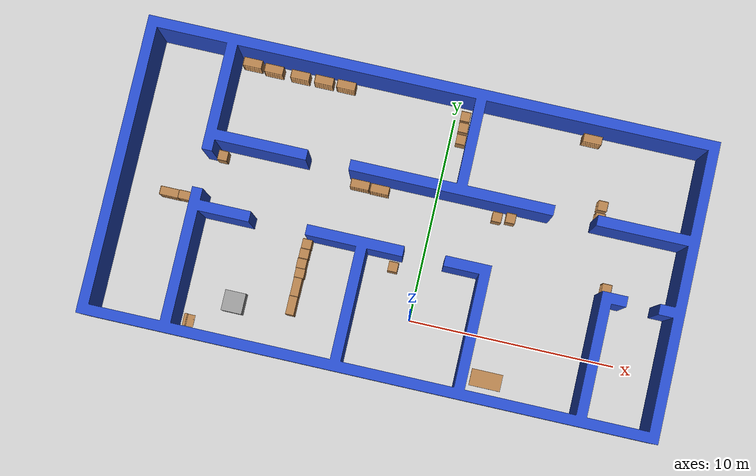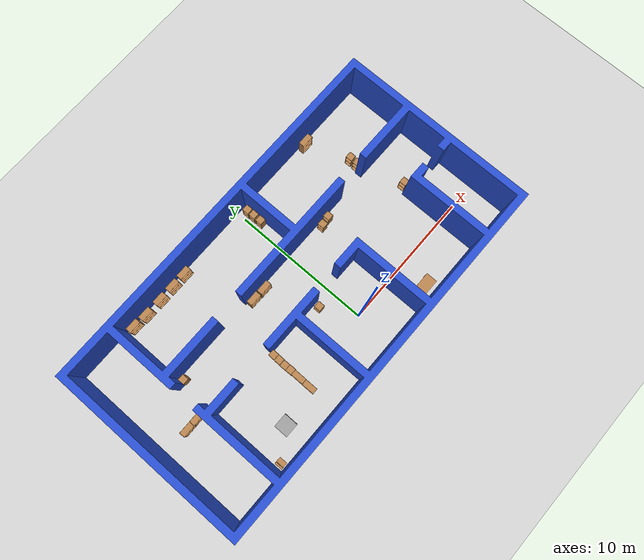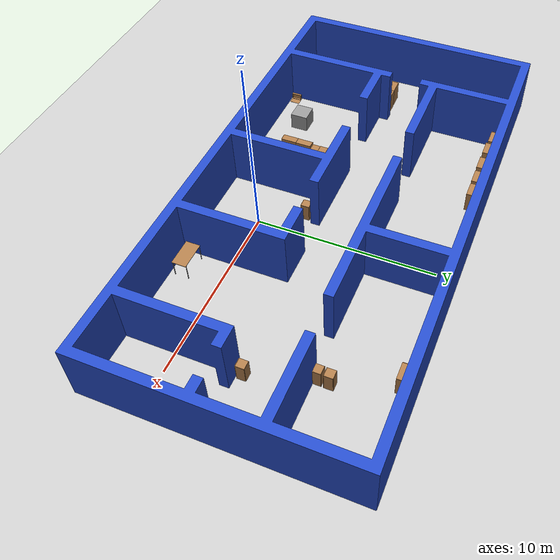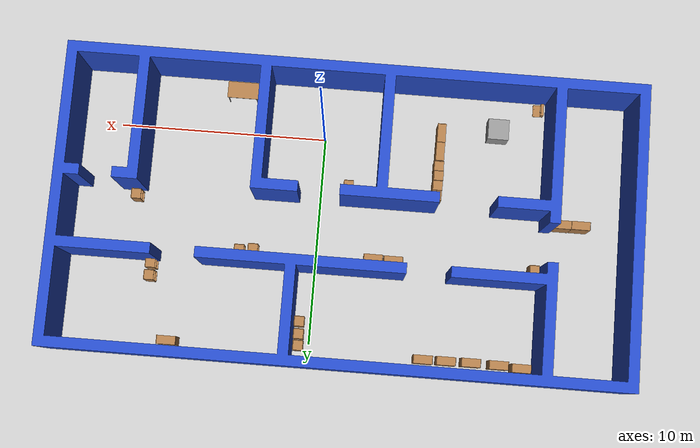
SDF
<sdf version="1.7">
 <world name="default">
  <light name="sun" type="directional">
   <pose>0 0 10 0 -0 0</pose>
   <diffuse>0.8 0.8 0.8 1</diffuse>
   <specular>0.2 0.2 0.2 1</specular>
   <attenuation>
    <range>1000</range>
    <constant>0.9</constant>
    <linear>0.01</linear>
    <quadratic>0.001</quadratic>
   </attenuation>
   <direction>-0.5 0.1 -0.9</direction>
   <spot><inner_angle>0</inner_angle><outer_angle>0</outer_angle><falloff>0</falloff></spot>
  </light>
  <model name="ground_plane">
   <static>1</static>
   <link name="link">
    <collision name="collision">
     <geometry><plane><normal>0 0 1</normal><size>100 100</size></plane></geometry>
     <surface>
      <contact><collide_bitmask>65535</collide_bitmask></contact>
      <friction><ode><mu>100</mu><mu2>50</mu2></ode></friction>
     </surface>
    </collision>
    <visual name="visual">
     <cast_shadows>0</cast_shadows>
     <geometry><plane><normal>0 0 1</normal><size>100 100</size></plane></geometry>
     <material>
      <script><uri>file://media/materials/scripts/gazebo.material</uri><name>Gazebo/Grey</name></script>
     </material>
    </visual>
   </link>
  </model>
  <gravity>0 0 -9.8</gravity>
  <magnetic_field>6e-06 2.3e-05 -4.2e-05</magnetic_field>
  <atmosphere type="adiabatic"/>
  <physics type="ode">
   <max_step_size>0.001</max_step_size>
   <real_time_factor>1</real_time_factor>
   <real_time_update_rate>1000</real_time_update_rate>
  </physics>
  <scene><ambient>0.4 0.4 0.4 1</ambient><background>0.7 0.7 0.7 1</background><shadows>1</shadows></scene>
  <spherical_coordinates>
   <surface_model>EARTH_WGS84</surface_model>
   <latitude_deg>0</latitude_deg>
   <longitude_deg>0</longitude_deg>
   <elevation>0</elevation>
   <heading_deg>0</heading_deg>
  </spherical_coordinates>
  <model name="office_better">
   <static>1</static>
   <frame name="object_frame"><pose relative_to="/world">0 0 0 0 -0 0</pose></frame>
   <pose relative_to="/world">32.0153 31.9937 31.8978 0 -0 0</pose>
   <link name="link">
    <pose>-32 -32 -32 0 -0 0</pose>
    <inertial>
     <mass>239.5</mass>
     <inertia>
      <ixx>6464.83</ixx>
      <ixy>225.633</ixy>
      <ixz>0</ixz>
      <iyy>19267</iyy>
      <iyz>0</iyz>
      <izz>25283.1</izz>
     </inertia>
     <pose relative_to="link_inertia_frame">-1.35 3.89 1.68 0 -0 0</pose>
     <frame name="link_inertia_frame"><pose relative_to="link_frame">0 0 0 0 -0 0</pose></frame>
    </inertial>
    <collision name="collision">
     <max_contacts>20</max_contacts>
     <pose relative_to="collision_frame">0 0 0 0 -0 0</pose>
     <geometry><mesh><uri>./model/office_better/meshes/mesh.stl</uri><scale>1 1 1</scale></mesh></geometry>
     <frame name="collision_frame"><pose relative_to="link_frame">0 0 0 0 -0 0</pose></frame>
    </collision>
    <visual name="visual">
     <pose relative_to="visual_frame">0 0 0 0 -0 0</pose>
     <material>
      <script><uri>file://media/materials/scripts/gazebo.material</uri><name>Gazebo/Blue</name></script>
      <shader type="vertex"><normal_map>__default__</normal_map></shader>
      <lighting>1</lighting>
      <ambient>0.15 0.75 0.35 1</ambient>
      <diffuse>0.1 0.95 0.25 1</diffuse>
      <specular>0.01 0.01 0.01 1</specular>
      <emissive>0 0 0 1</emissive>
     </material>
     <geometry><mesh><uri>./model/office_better/meshes/mesh.stl</uri><scale>1 1 1</scale></mesh></geometry>
     <frame name="visual_frame"><pose relative_to="link_frame">0 0 0 0 -0 0</pose></frame>
    </visual>
    <frame name="link_frame"><pose relative_to="object_frame">0 0 0 0 -0 0</pose></frame>
   </link>
  </model>
  <model name="bookshelf">
   <static>1</static>
   <link name="link">
    <inertial><mass>1</mass></inertial>
    <collision name="back">
     <pose>0 0.005 0.6 0 -0 0</pose>
     <geometry><box><size>0.9 0.01 1.2</size></box></geometry>
    </collision>
    <visual name="visual1">
     <pose>0 0.005 0.6 0 -0 0</pose>
     <geometry><box><size>0.9 0.01 1.2</size></box></geometry>
     <material>
      <script><uri>file://media/materials/scripts/gazebo.material</uri><name>Gazebo/Wood</name></script>
     </material>
    </visual>
    <collision name="left_side">
     <pose>0.45 -0.195 0.6 0 -0 0</pose>
     <geometry><box><size>0.02 0.4 1.2</size></box></geometry>
    </collision>
    <visual name="visual2">
     <pose>0.45 -0.195 0.6 0 -0 0</pose>
     <geometry><box><size>0.02 0.4 1.2</size></box></geometry>
     <material>
      <script><uri>file://media/materials/scripts/gazebo.material</uri><name>Gazebo/Wood</name></script>
     </material>
    </visual>
    <collision name="right_side">
     <pose>-0.45 -0.195 0.6 0 -0 0</pose>
     <geometry><box><size>0.02 0.4 1.2</size></box></geometry>
    </collision>
    <visual name="visual3">
     <pose>-0.45 -0.195 0.6 0 -0 0</pose>
     <geometry><box><size>0.02 0.4 1.2</size></box></geometry>
     <material>
      <script><uri>file://media/materials/scripts/gazebo.material</uri><name>Gazebo/Wood</name></script>
     </material>
    </visual>
    <collision name="bottom">
     <pose>0 -0.195 0.03 0 -0 0</pose>
     <geometry><box><size>0.88 0.4 0.06</size></box></geometry>
    </collision>
    <visual name="visual4">
     <pose>0 -0.195 0.03 0 -0 0</pose>
     <geometry><box><size>0.88 0.4 0.06</size></box></geometry>
     <material>
      <script><uri>file://media/materials/scripts/gazebo.material</uri><name>Gazebo/Wood</name></script>
     </material>
    </visual>
    <collision name="top">
     <pose>0 -0.195 1.19 0 -0 0</pose>
     <geometry><box><size>0.88 0.4 0.02</size></box></geometry>
    </collision>
    <visual name="visual5">
     <pose>0 -0.195 1.19 0 -0 0</pose>
     <geometry><box><size>0.88 0.4 0.02</size></box></geometry>
     <material>
      <script><uri>file://media/materials/scripts/gazebo.material</uri><name>Gazebo/Wood</name></script>
     </material>
    </visual>
    <collision name="low_shelf">
     <pose>0 -0.195 0.43 0 -0 0</pose>
     <geometry><box><size>0.88 0.4 0.02</size></box></geometry>
    </collision>
    <visual name="visual6">
     <pose>0 -0.195 0.43 0 -0 0</pose>
     <geometry><box><size>0.88 0.4 0.02</size></box></geometry>
     <material>
      <script><uri>file://media/materials/scripts/gazebo.material</uri><name>Gazebo/Wood</name></script>
     </material>
    </visual>
    <collision name="high_shelf">
     <pose>0 -0.195 0.8 0 -0 0</pose>
     <geometry><box><size>0.88 0.4 0.02</size></box></geometry>
    </collision>
    <visual name="visual7">
     <pose>0 -0.195 0.8 0 -0 0</pose>
     <geometry><box><size>0.88 0.4 0.02</size></box></geometry>
     <material>
      <script><uri>file://media/materials/scripts/gazebo.material</uri><name>Gazebo/Wood</name></script>
     </material>
    </visual>
   </link>
   <pose>-10.0788 10.5753 0 0 -0 0</pose>
  </model>
  <model name="bookshelf_0">
   <static>1</static>
   <link name="link">
    <inertial><mass>1</mass></inertial>
    <collision name="back">
     <pose>0 0.005 0.6 0 -0 0</pose>
     <geometry><box><size>0.9 0.01 1.2</size></box></geometry>
    </collision>
    <visual name="visual1">
     <pose>0 0.005 0.6 0 -0 0</pose>
     <geometry><box><size>0.9 0.01 1.2</size></box></geometry>
     <material>
      <script><uri>file://media/materials/scripts/gazebo.material</uri><name>Gazebo/Wood</name></script>
     </material>
    </visual>
    <collision name="left_side">
     <pose>0.45 -0.195 0.6 0 -0 0</pose>
     <geometry><box><size>0.02 0.4 1.2</size></box></geometry>
    </collision>
    <visual name="visual2">
     <pose>0.45 -0.195 0.6 0 -0 0</pose>
     <geometry><box><size>0.02 0.4 1.2</size></box></geometry>
     <material>
      <script><uri>file://media/materials/scripts/gazebo.material</uri><name>Gazebo/Wood</name></script>
     </material>
    </visual>
    <collision name="right_side">
     <pose>-0.45 -0.195 0.6 0 -0 0</pose>
     <geometry><box><size>0.02 0.4 1.2</size></box></geometry>
    </collision>
    <visual name="visual3">
     <pose>-0.45 -0.195 0.6 0 -0 0</pose>
     <geometry><box><size>0.02 0.4 1.2</size></box></geometry>
     <material>
      <script><uri>file://media/materials/scripts/gazebo.material</uri><name>Gazebo/Wood</name></script>
     </material>
    </visual>
    <collision name="bottom">
     <pose>0 -0.195 0.03 0 -0 0</pose>
     <geometry><box><size>0.88 0.4 0.06</size></box></geometry>
    </collision>
    <visual name="visual4">
     <pose>0 -0.195 0.03 0 -0 0</pose>
     <geometry><box><size>0.88 0.4 0.06</size></box></geometry>
     <material>
      <script><uri>file://media/materials/scripts/gazebo.material</uri><name>Gazebo/Wood</name></script>
     </material>
    </visual>
    <collision name="top">
     <pose>0 -0.195 1.19 0 -0 0</pose>
     <geometry><box><size>0.88 0.4 0.02</size></box></geometry>
    </collision>
    <visual name="visual5">
     <pose>0 -0.195 1.19 0 -0 0</pose>
     <geometry><box><size>0.88 0.4 0.02</size></box></geometry>
     <material>
      <script><uri>file://media/materials/scripts/gazebo.material</uri><name>Gazebo/Wood</name></script>
     </material>
    </visual>
    <collision name="low_shelf">
     <pose>0 -0.195 0.43 0 -0 0</pose>
     <geometry><box><size>0.88 0.4 0.02</size></box></geometry>
    </collision>
    <visual name="visual6">
     <pose>0 -0.195 0.43 0 -0 0</pose>
     <geometry><box><size>0.88 0.4 0.02</size></box></geometry>
     <material>
      <script><uri>file://media/materials/scripts/gazebo.material</uri><name>Gazebo/Wood</name></script>
     </material>
    </visual>
    <collision name="high_shelf">
     <pose>0 -0.195 0.8 0 -0 0</pose>
     <geometry><box><size>0.88 0.4 0.02</size></box></geometry>
    </collision>
    <visual name="visual7">
     <pose>0 -0.195 0.8 0 -0 0</pose>
     <geometry><box><size>0.88 0.4 0.02</size></box></geometry>
     <material>
      <script><uri>file://media/materials/scripts/gazebo.material</uri><name>Gazebo/Wood</name></script>
     </material>
    </visual>
   </link>
   <pose>-9.01072 10.5031 0 0 -0 0</pose>
  </model>
  <model name="bookshelf_1">
   <static>1</static>
   <link name="link">
    <inertial><mass>1</mass></inertial>
    <collision name="back">
     <pose>0 0.005 0.6 0 -0 0</pose>
     <geometry><box><size>0.9 0.01 1.2</size></box></geometry>
    </collision>
    <visual name="visual1">
     <pose>0 0.005 0.6 0 -0 0</pose>
     <geometry><box><size>0.9 0.01 1.2</size></box></geometry>
     <material>
      <script><uri>file://media/materials/scripts/gazebo.material</uri><name>Gazebo/Wood</name></script>
     </material>
    </visual>
    <collision name="left_side">
     <pose>0.45 -0.195 0.6 0 -0 0</pose>
     <geometry><box><size>0.02 0.4 1.2</size></box></geometry>
    </collision>
    <visual name="visual2">
     <pose>0.45 -0.195 0.6 0 -0 0</pose>
     <geometry><box><size>0.02 0.4 1.2</size></box></geometry>
     <material>
      <script><uri>file://media/materials/scripts/gazebo.material</uri><name>Gazebo/Wood</name></script>
     </material>
    </visual>
    <collision name="right_side">
     <pose>-0.45 -0.195 0.6 0 -0 0</pose>
     <geometry><box><size>0.02 0.4 1.2</size></box></geometry>
    </collision>
    <visual name="visual3">
     <pose>-0.45 -0.195 0.6 0 -0 0</pose>
     <geometry><box><size>0.02 0.4 1.2</size></box></geometry>
     <material>
      <script><uri>file://media/materials/scripts/gazebo.material</uri><name>Gazebo/Wood</name></script>
     </material>
    </visual>
    <collision name="bottom">
     <pose>0 -0.195 0.03 0 -0 0</pose>
     <geometry><box><size>0.88 0.4 0.06</size></box></geometry>
    </collision>
    <visual name="visual4">
     <pose>0 -0.195 0.03 0 -0 0</pose>
     <geometry><box><size>0.88 0.4 0.06</size></box></geometry>
     <material>
      <script><uri>file://media/materials/scripts/gazebo.material</uri><name>Gazebo/Wood</name></script>
     </material>
    </visual>
    <collision name="top">
     <pose>0 -0.195 1.19 0 -0 0</pose>
     <geometry><box><size>0.88 0.4 0.02</size></box></geometry>
    </collision>
    <visual name="visual5">
     <pose>0 -0.195 1.19 0 -0 0</pose>
     <geometry><box><size>0.88 0.4 0.02</size></box></geometry>
     <material>
      <script><uri>file://media/materials/scripts/gazebo.material</uri><name>Gazebo/Wood</name></script>
     </material>
    </visual>
    <collision name="low_shelf">
     <pose>0 -0.195 0.43 0 -0 0</pose>
     <geometry><box><size>0.88 0.4 0.02</size></box></geometry>
    </collision>
    <visual name="visual6">
     <pose>0 -0.195 0.43 0 -0 0</pose>
     <geometry><box><size>0.88 0.4 0.02</size></box></geometry>
     <material>
      <script><uri>file://media/materials/scripts/gazebo.material</uri><name>Gazebo/Wood</name></script>
     </material>
    </visual>
    <collision name="high_shelf">
     <pose>0 -0.195 0.8 0 -0 0</pose>
     <geometry><box><size>0.88 0.4 0.02</size></box></geometry>
    </collision>
    <visual name="visual7">
     <pose>0 -0.195 0.8 0 -0 0</pose>
     <geometry><box><size>0.88 0.4 0.02</size></box></geometry>
     <material>
      <script><uri>file://media/materials/scripts/gazebo.material</uri><name>Gazebo/Wood</name></script>
     </material>
    </visual>
   </link>
   <pose>-7.70566 10.4883 0 0 -0 0</pose>
  </model>
  <model name="bookshelf_2">
   <static>1</static>
   <link name="link">
    <inertial><mass>1</mass></inertial>
    <collision name="back">
     <pose>0 0.005 0.6 0 -0 0</pose>
     <geometry><box><size>0.9 0.01 1.2</size></box></geometry>
    </collision>
    <visual name="visual1">
     <pose>0 0.005 0.6 0 -0 0</pose>
     <geometry><box><size>0.9 0.01 1.2</size></box></geometry>
     <material>
      <script><uri>file://media/materials/scripts/gazebo.material</uri><name>Gazebo/Wood</name></script>
     </material>
    </visual>
    <collision name="left_side">
     <pose>0.45 -0.195 0.6 0 -0 0</pose>
     <geometry><box><size>0.02 0.4 1.2</size></box></geometry>
    </collision>
    <visual name="visual2">
     <pose>0.45 -0.195 0.6 0 -0 0</pose>
     <geometry><box><size>0.02 0.4 1.2</size></box></geometry>
     <material>
      <script><uri>file://media/materials/scripts/gazebo.material</uri><name>Gazebo/Wood</name></script>
     </material>
    </visual>
    <collision name="right_side">
     <pose>-0.45 -0.195 0.6 0 -0 0</pose>
     <geometry><box><size>0.02 0.4 1.2</size></box></geometry>
    </collision>
    <visual name="visual3">
     <pose>-0.45 -0.195 0.6 0 -0 0</pose>
     <geometry><box><size>0.02 0.4 1.2</size></box></geometry>
     <material>
      <script><uri>file://media/materials/scripts/gazebo.material</uri><name>Gazebo/Wood</name></script>
     </material>
    </visual>
    <collision name="bottom">
     <pose>0 -0.195 0.03 0 -0 0</pose>
     <geometry><box><size>0.88 0.4 0.06</size></box></geometry>
    </collision>
    <visual name="visual4">
     <pose>0 -0.195 0.03 0 -0 0</pose>
     <geometry><box><size>0.88 0.4 0.06</size></box></geometry>
     <material>
      <script><uri>file://media/materials/scripts/gazebo.material</uri><name>Gazebo/Wood</name></script>
     </material>
    </visual>
    <collision name="top">
     <pose>0 -0.195 1.19 0 -0 0</pose>
     <geometry><box><size>0.88 0.4 0.02</size></box></geometry>
    </collision>
    <visual name="visual5">
     <pose>0 -0.195 1.19 0 -0 0</pose>
     <geometry><box><size>0.88 0.4 0.02</size></box></geometry>
     <material>
      <script><uri>file://media/materials/scripts/gazebo.material</uri><name>Gazebo/Wood</name></script>
     </material>
    </visual>
    <collision name="low_shelf">
     <pose>0 -0.195 0.43 0 -0 0</pose>
     <geometry><box><size>0.88 0.4 0.02</size></box></geometry>
    </collision>
    <visual name="visual6">
     <pose>0 -0.195 0.43 0 -0 0</pose>
     <geometry><box><size>0.88 0.4 0.02</size></box></geometry>
     <material>
      <script><uri>file://media/materials/scripts/gazebo.material</uri><name>Gazebo/Wood</name></script>
     </material>
    </visual>
    <collision name="high_shelf">
     <pose>0 -0.195 0.8 0 -0 0</pose>
     <geometry><box><size>0.88 0.4 0.02</size></box></geometry>
    </collision>
    <visual name="visual7">
     <pose>0 -0.195 0.8 0 -0 0</pose>
     <geometry><box><size>0.88 0.4 0.02</size></box></geometry>
     <material>
      <script><uri>file://media/materials/scripts/gazebo.material</uri><name>Gazebo/Wood</name></script>
     </material>
    </visual>
   </link>
   <pose>-6.53518 10.5005 0 0 -0 0</pose>
  </model>
  <model name="bookshelf_3">
   <static>1</static>
   <link name="link">
    <inertial><mass>1</mass></inertial>
    <collision name="back">
     <pose>0 0.005 0.6 0 -0 0</pose>
     <geometry><box><size>0.9 0.01 1.2</size></box></geometry>
    </collision>
    <visual name="visual1">
     <pose>0 0.005 0.6 0 -0 0</pose>
     <geometry><box><size>0.9 0.01 1.2</size></box></geometry>
     <material>
      <script><uri>file://media/materials/scripts/gazebo.material</uri><name>Gazebo/Wood</name></script>
     </material>
    </visual>
    <collision name="left_side">
     <pose>0.45 -0.195 0.6 0 -0 0</pose>
     <geometry><box><size>0.02 0.4 1.2</size></box></geometry>
    </collision>
    <visual name="visual2">
     <pose>0.45 -0.195 0.6 0 -0 0</pose>
     <geometry><box><size>0.02 0.4 1.2</size></box></geometry>
     <material>
      <script><uri>file://media/materials/scripts/gazebo.material</uri><name>Gazebo/Wood</name></script>
     </material>
    </visual>
    <collision name="right_side">
     <pose>-0.45 -0.195 0.6 0 -0 0</pose>
     <geometry><box><size>0.02 0.4 1.2</size></box></geometry>
    </collision>
    <visual name="visual3">
     <pose>-0.45 -0.195 0.6 0 -0 0</pose>
     <geometry><box><size>0.02 0.4 1.2</size></box></geometry>
     <material>
      <script><uri>file://media/materials/scripts/gazebo.material</uri><name>Gazebo/Wood</name></script>
     </material>
    </visual>
    <collision name="bottom">
     <pose>0 -0.195 0.03 0 -0 0</pose>
     <geometry><box><size>0.88 0.4 0.06</size></box></geometry>
    </collision>
    <visual name="visual4">
     <pose>0 -0.195 0.03 0 -0 0</pose>
     <geometry><box><size>0.88 0.4 0.06</size></box></geometry>
     <material>
      <script><uri>file://media/materials/scripts/gazebo.material</uri><name>Gazebo/Wood</name></script>
     </material>
    </visual>
    <collision name="top">
     <pose>0 -0.195 1.19 0 -0 0</pose>
     <geometry><box><size>0.88 0.4 0.02</size></box></geometry>
    </collision>
    <visual name="visual5">
     <pose>0 -0.195 1.19 0 -0 0</pose>
     <geometry><box><size>0.88 0.4 0.02</size></box></geometry>
     <material>
      <script><uri>file://media/materials/scripts/gazebo.material</uri><name>Gazebo/Wood</name></script>
     </material>
    </visual>
    <collision name="low_shelf">
     <pose>0 -0.195 0.43 0 -0 0</pose>
     <geometry><box><size>0.88 0.4 0.02</size></box></geometry>
    </collision>
    <visual name="visual6">
     <pose>0 -0.195 0.43 0 -0 0</pose>
     <geometry><box><size>0.88 0.4 0.02</size></box></geometry>
     <material>
      <script><uri>file://media/materials/scripts/gazebo.material</uri><name>Gazebo/Wood</name></script>
     </material>
    </visual>
    <collision name="high_shelf">
     <pose>0 -0.195 0.8 0 -0 0</pose>
     <geometry><box><size>0.88 0.4 0.02</size></box></geometry>
    </collision>
    <visual name="visual7">
     <pose>0 -0.195 0.8 0 -0 0</pose>
     <geometry><box><size>0.88 0.4 0.02</size></box></geometry>
     <material>
      <script><uri>file://media/materials/scripts/gazebo.material</uri><name>Gazebo/Wood</name></script>
     </material>
    </visual>
   </link>
   <pose>-5.4445 10.5119 0 0 -0 0</pose>
  </model>
  <model name="cabinet">
   <static>1</static>
   <link name="cabinet_bottom_plate">
    <inertial>
     <pose>0 0 -1 0 -0 0</pose>
     <inertia><ixx>2.05</ixx><ixy>0</ixy><ixz>0</ixz><iyy>2.05</iyy><iyz>0</iyz><izz>2.05</izz></inertia>
     <mass>25</mass>
    </inertial>
    <collision name="cabinet_bottom_plate_geom">
     <pose>0 0 0.01 0 -0 0</pose>
     <geometry><box><size>0.45 0.45 0.02</size></box></geometry>
    </collision>
    <visual name="cabinet_bottom_plate_geom_visual">
     <pose>0 0 0.01 0 -0 0</pose>
     <geometry><box><size>0.45 0.45 0.02</size></box></geometry>
     <material>
      <script><uri>file://media/materials/scripts/gazebo.material</uri><name>Gazebo/Wood</name></script>
     </material>
    </visual>
    <collision name="cabinet_bottom_plate_geom_cabinet_back_plate">
     <pose>0.235 0 0.51 0 -0 0</pose>
     <geometry><box><size>0.02 0.45 1.02</size></box></geometry>
    </collision>
    <visual name="cabinet_bottom_plate_geom_cabinet_back_plate_visual">
     <pose>0.235 0 0.51 0 -0 0</pose>
     <geometry><box><size>0.02 0.45 1.02</size></box></geometry>
     <material>
      <script><uri>file://media/materials/scripts/gazebo.material</uri><name>Gazebo/Wood</name></script>
     </material>
    </visual>
    <collision name="cabinet_bottom_plate_geom_cabinet_left_plate">
     <pose>0 0.235 0.51 0 -0 0</pose>
     <geometry><box><size>0.45 0.02 1.02</size></box></geometry>
    </collision>
    <visual name="cabinet_bottom_plate_geom_cabinet_left_plate_visual">
     <pose>0 0.235 0.51 0 -0 0</pose>
     <geometry><box><size>0.45 0.02 1.02</size></box></geometry>
     <material>
      <script><uri>file://media/materials/scripts/gazebo.material</uri><name>Gazebo/Wood</name></script>
     </material>
    </visual>
    <collision name="cabinet_bottom_plate_geom_cabinet_middle_plate">
     <pose>0 0 0.51 0 -0 0</pose>
     <geometry><box><size>0.45 0.45 0.02</size></box></geometry>
    </collision>
    <visual name="cabinet_bottom_plate_geom_cabinet_middle_plate_visual">
     <pose>0 0 0.51 0 -0 0</pose>
     <geometry><box><size>0.45 0.45 0.02</size></box></geometry>
     <material>
      <script><uri>file://media/materials/scripts/gazebo.material</uri><name>Gazebo/Wood</name></script>
     </material>
    </visual>
    <collision name="cabinet_bottom_plate_geom_cabinet_right_plate">
     <pose>0 -0.235 0.51 0 -0 0</pose>
     <geometry><box><size>0.45 0.02 1.02</size></box></geometry>
    </collision>
    <visual name="cabinet_bottom_plate_geom_cabinet_right_plate_visual">
     <pose>0 -0.235 0.51 0 -0 0</pose>
     <geometry><box><size>0.45 0.02 1.02</size></box></geometry>
     <material>
      <script><uri>file://media/materials/scripts/gazebo.material</uri><name>Gazebo/Wood</name></script>
     </material>
    </visual>
    <collision name="cabinet_bottom_plate_geom_cabinet_top_plate">
     <pose>0 0 1.01 0 -0 0</pose>
     <geometry><box><size>0.45 0.45 0.02</size></box></geometry>
    </collision>
    <visual name="cabinet_bottom_plate_geom_cabinet_top_plate_visual">
     <pose>0 0 1.01 0 -0 0</pose>
     <geometry><box><size>0.45 0.45 0.02</size></box></geometry>
     <material>
      <script><uri>file://media/materials/scripts/gazebo.material</uri><name>Gazebo/Wood</name></script>
     </material>
    </visual>
   </link>
   <pose>-10.4654 5.70058 0 0 -0 0</pose>
  </model>
  <model name="cabinet_0">
   <static>1</static>
   <link name="cabinet_bottom_plate">
    <inertial>
     <pose>0 0 -1 0 -0 0</pose>
     <inertia><ixx>2.05</ixx><ixy>0</ixy><ixz>0</ixz><iyy>2.05</iyy><iyz>0</iyz><izz>2.05</izz></inertia>
     <mass>25</mass>
    </inertial>
    <collision name="cabinet_bottom_plate_geom">
     <pose>0 0 0.01 0 -0 0</pose>
     <geometry><box><size>0.45 0.45 0.02</size></box></geometry>
    </collision>
    <visual name="cabinet_bottom_plate_geom_visual">
     <pose>0 0 0.01 0 -0 0</pose>
     <geometry><box><size>0.45 0.45 0.02</size></box></geometry>
     <material>
      <script><uri>file://media/materials/scripts/gazebo.material</uri><name>Gazebo/Wood</name></script>
     </material>
    </visual>
    <collision name="cabinet_bottom_plate_geom_cabinet_back_plate">
     <pose>0.235 0 0.51 0 -0 0</pose>
     <geometry><box><size>0.02 0.45 1.02</size></box></geometry>
    </collision>
    <visual name="cabinet_bottom_plate_geom_cabinet_back_plate_visual">
     <pose>0.235 0 0.51 0 -0 0</pose>
     <geometry><box><size>0.02 0.45 1.02</size></box></geometry>
     <material>
      <script><uri>file://media/materials/scripts/gazebo.material</uri><name>Gazebo/Wood</name></script>
     </material>
    </visual>
    <collision name="cabinet_bottom_plate_geom_cabinet_left_plate">
     <pose>0 0.235 0.51 0 -0 0</pose>
     <geometry><box><size>0.45 0.02 1.02</size></box></geometry>
    </collision>
    <visual name="cabinet_bottom_plate_geom_cabinet_left_plate_visual">
     <pose>0 0.235 0.51 0 -0 0</pose>
     <geometry><box><size>0.45 0.02 1.02</size></box></geometry>
     <material>
      <script><uri>file://media/materials/scripts/gazebo.material</uri><name>Gazebo/Wood</name></script>
     </material>
    </visual>
    <collision name="cabinet_bottom_plate_geom_cabinet_middle_plate">
     <pose>0 0 0.51 0 -0 0</pose>
     <geometry><box><size>0.45 0.45 0.02</size></box></geometry>
    </collision>
    <visual name="cabinet_bottom_plate_geom_cabinet_middle_plate_visual">
     <pose>0 0 0.51 0 -0 0</pose>
     <geometry><box><size>0.45 0.45 0.02</size></box></geometry>
     <material>
      <script><uri>file://media/materials/scripts/gazebo.material</uri><name>Gazebo/Wood</name></script>
     </material>
    </visual>
    <collision name="cabinet_bottom_plate_geom_cabinet_right_plate">
     <pose>0 -0.235 0.51 0 -0 0</pose>
     <geometry><box><size>0.45 0.02 1.02</size></box></geometry>
    </collision>
    <visual name="cabinet_bottom_plate_geom_cabinet_right_plate_visual">
     <pose>0 -0.235 0.51 0 -0 0</pose>
     <geometry><box><size>0.45 0.02 1.02</size></box></geometry>
     <material>
      <script><uri>file://media/materials/scripts/gazebo.material</uri><name>Gazebo/Wood</name></script>
     </material>
    </visual>
    <collision name="cabinet_bottom_plate_geom_cabinet_top_plate">
     <pose>0 0 1.01 0 -0 0</pose>
     <geometry><box><size>0.45 0.45 0.02</size></box></geometry>
    </collision>
    <visual name="cabinet_bottom_plate_geom_cabinet_top_plate_visual">
     <pose>0 0 1.01 0 -0 0</pose>
     <geometry><box><size>0.45 0.45 0.02</size></box></geometry>
     <material>
      <script><uri>file://media/materials/scripts/gazebo.material</uri><name>Gazebo/Wood</name></script>
     </material>
    </visual>
   </link>
   <pose>3.65099 5.79416 0 0 -0 0</pose>
  </model>
  <model name="cabinet_1">
   <static>1</static>
   <link name="cabinet_bottom_plate">
    <inertial>
     <pose>0 0 -1 0 -0 0</pose>
     <inertia><ixx>2.05</ixx><ixy>0</ixy><ixz>0</ixz><iyy>2.05</iyy><iyz>0</iyz><izz>2.05</izz></inertia>
     <mass>25</mass>
    </inertial>
    <collision name="cabinet_bottom_plate_geom">
     <pose>0 0 0.01 0 -0 0</pose>
     <geometry><box><size>0.45 0.45 0.02</size></box></geometry>
    </collision>
    <visual name="cabinet_bottom_plate_geom_visual">
     <pose>0 0 0.01 0 -0 0</pose>
     <geometry><box><size>0.45 0.45 0.02</size></box></geometry>
     <material>
      <script><uri>file://media/materials/scripts/gazebo.material</uri><name>Gazebo/Wood</name></script>
     </material>
    </visual>
    <collision name="cabinet_bottom_plate_geom_cabinet_back_plate">
     <pose>0.235 0 0.51 0 -0 0</pose>
     <geometry><box><size>0.02 0.45 1.02</size></box></geometry>
    </collision>
    <visual name="cabinet_bottom_plate_geom_cabinet_back_plate_visual">
     <pose>0.235 0 0.51 0 -0 0</pose>
     <geometry><box><size>0.02 0.45 1.02</size></box></geometry>
     <material>
      <script><uri>file://media/materials/scripts/gazebo.material</uri><name>Gazebo/Wood</name></script>
     </material>
    </visual>
    <collision name="cabinet_bottom_plate_geom_cabinet_left_plate">
     <pose>0 0.235 0.51 0 -0 0</pose>
     <geometry><box><size>0.45 0.02 1.02</size></box></geometry>
    </collision>
    <visual name="cabinet_bottom_plate_geom_cabinet_left_plate_visual">
     <pose>0 0.235 0.51 0 -0 0</pose>
     <geometry><box><size>0.45 0.02 1.02</size></box></geometry>
     <material>
      <script><uri>file://media/materials/scripts/gazebo.material</uri><name>Gazebo/Wood</name></script>
     </material>
    </visual>
    <collision name="cabinet_bottom_plate_geom_cabinet_middle_plate">
     <pose>0 0 0.51 0 -0 0</pose>
     <geometry><box><size>0.45 0.45 0.02</size></box></geometry>
    </collision>
    <visual name="cabinet_bottom_plate_geom_cabinet_middle_plate_visual">
     <pose>0 0 0.51 0 -0 0</pose>
     <geometry><box><size>0.45 0.45 0.02</size></box></geometry>
     <material>
      <script><uri>file://media/materials/scripts/gazebo.material</uri><name>Gazebo/Wood</name></script>
     </material>
    </visual>
    <collision name="cabinet_bottom_plate_geom_cabinet_right_plate">
     <pose>0 -0.235 0.51 0 -0 0</pose>
     <geometry><box><size>0.45 0.02 1.02</size></box></geometry>
    </collision>
    <visual name="cabinet_bottom_plate_geom_cabinet_right_plate_visual">
     <pose>0 -0.235 0.51 0 -0 0</pose>
     <geometry><box><size>0.45 0.02 1.02</size></box></geometry>
     <material>
      <script><uri>file://media/materials/scripts/gazebo.material</uri><name>Gazebo/Wood</name></script>
     </material>
    </visual>
    <collision name="cabinet_bottom_plate_geom_cabinet_top_plate">
     <pose>0 0 1.01 0 -0 0</pose>
     <geometry><box><size>0.45 0.45 0.02</size></box></geometry>
    </collision>
    <visual name="cabinet_bottom_plate_geom_cabinet_top_plate_visual">
     <pose>0 0 1.01 0 -0 0</pose>
     <geometry><box><size>0.45 0.45 0.02</size></box></geometry>
     <material>
      <script><uri>file://media/materials/scripts/gazebo.material</uri><name>Gazebo/Wood</name></script>
     </material>
    </visual>
   </link>
   <pose>2.99721 5.70704 0 0 -0 0</pose>
  </model>
  <model name="cabinet_2">
   <static>1</static>
   <link name="cabinet_bottom_plate">
    <inertial>
     <pose>0 0 -1 0 -0 0</pose>
     <inertia><ixx>2.05</ixx><ixy>0</ixy><ixz>0</ixz><iyy>2.05</iyy><iyz>0</iyz><izz>2.05</izz></inertia>
     <mass>25</mass>
    </inertial>
    <collision name="cabinet_bottom_plate_geom">
     <pose>0 0 0.01 0 -0 0</pose>
     <geometry><box><size>0.45 0.45 0.02</size></box></geometry>
    </collision>
    <visual name="cabinet_bottom_plate_geom_visual">
     <pose>0 0 0.01 0 -0 0</pose>
     <geometry><box><size>0.45 0.45 0.02</size></box></geometry>
     <material>
      <script><uri>file://media/materials/scripts/gazebo.material</uri><name>Gazebo/Wood</name></script>
     </material>
    </visual>
    <collision name="cabinet_bottom_plate_geom_cabinet_back_plate">
     <pose>0.235 0 0.51 0 -0 0</pose>
     <geometry><box><size>0.02 0.45 1.02</size></box></geometry>
    </collision>
    <visual name="cabinet_bottom_plate_geom_cabinet_back_plate_visual">
     <pose>0.235 0 0.51 0 -0 0</pose>
     <geometry><box><size>0.02 0.45 1.02</size></box></geometry>
     <material>
      <script><uri>file://media/materials/scripts/gazebo.material</uri><name>Gazebo/Wood</name></script>
     </material>
    </visual>
    <collision name="cabinet_bottom_plate_geom_cabinet_left_plate">
     <pose>0 0.235 0.51 0 -0 0</pose>
     <geometry><box><size>0.45 0.02 1.02</size></box></geometry>
    </collision>
    <visual name="cabinet_bottom_plate_geom_cabinet_left_plate_visual">
     <pose>0 0.235 0.51 0 -0 0</pose>
     <geometry><box><size>0.45 0.02 1.02</size></box></geometry>
     <material>
      <script><uri>file://media/materials/scripts/gazebo.material</uri><name>Gazebo/Wood</name></script>
     </material>
    </visual>
    <collision name="cabinet_bottom_plate_geom_cabinet_middle_plate">
     <pose>0 0 0.51 0 -0 0</pose>
     <geometry><box><size>0.45 0.45 0.02</size></box></geometry>
    </collision>
    <visual name="cabinet_bottom_plate_geom_cabinet_middle_plate_visual">
     <pose>0 0 0.51 0 -0 0</pose>
     <geometry><box><size>0.45 0.45 0.02</size></box></geometry>
     <material>
      <script><uri>file://media/materials/scripts/gazebo.material</uri><name>Gazebo/Wood</name></script>
     </material>
    </visual>
    <collision name="cabinet_bottom_plate_geom_cabinet_right_plate">
     <pose>0 -0.235 0.51 0 -0 0</pose>
     <geometry><box><size>0.45 0.02 1.02</size></box></geometry>
    </collision>
    <visual name="cabinet_bottom_plate_geom_cabinet_right_plate_visual">
     <pose>0 -0.235 0.51 0 -0 0</pose>
     <geometry><box><size>0.45 0.02 1.02</size></box></geometry>
     <material>
      <script><uri>file://media/materials/scripts/gazebo.material</uri><name>Gazebo/Wood</name></script>
     </material>
    </visual>
    <collision name="cabinet_bottom_plate_geom_cabinet_top_plate">
     <pose>0 0 1.01 0 -0 0</pose>
     <geometry><box><size>0.45 0.45 0.02</size></box></geometry>
    </collision>
    <visual name="cabinet_bottom_plate_geom_cabinet_top_plate_visual">
     <pose>0 0 1.01 0 -0 0</pose>
     <geometry><box><size>0.45 0.45 0.02</size></box></geometry>
     <material>
      <script><uri>file://media/materials/scripts/gazebo.material</uri><name>Gazebo/Wood</name></script>
     </material>
    </visual>
   </link>
   <pose>8.81846 3.4909 0 0 -0 0</pose>
  </model>
  <model name="cabinet_3">
   <static>1</static>
   <link name="cabinet_bottom_plate">
    <inertial>
     <pose>0 0 -1 0 -0 0</pose>
     <inertia><ixx>2.05</ixx><ixy>0</ixy><ixz>0</ixz><iyy>2.05</iyy><iyz>0</iyz><izz>2.05</izz></inertia>
     <mass>25</mass>
    </inertial>
    <collision name="cabinet_bottom_plate_geom">
     <pose>0 0 0.01 0 -0 0</pose>
     <geometry><box><size>0.45 0.45 0.02</size></box></geometry>
    </collision>
    <visual name="cabinet_bottom_plate_geom_visual">
     <pose>0 0 0.01 0 -0 0</pose>
     <geometry><box><size>0.45 0.45 0.02</size></box></geometry>
     <material>
      <script><uri>file://media/materials/scripts/gazebo.material</uri><name>Gazebo/Wood</name></script>
     </material>
    </visual>
    <collision name="cabinet_bottom_plate_geom_cabinet_back_plate">
     <pose>0.235 0 0.51 0 -0 0</pose>
     <geometry><box><size>0.02 0.45 1.02</size></box></geometry>
    </collision>
    <visual name="cabinet_bottom_plate_geom_cabinet_back_plate_visual">
     <pose>0.235 0 0.51 0 -0 0</pose>
     <geometry><box><size>0.02 0.45 1.02</size></box></geometry>
     <material>
      <script><uri>file://media/materials/scripts/gazebo.material</uri><name>Gazebo/Wood</name></script>
     </material>
    </visual>
    <collision name="cabinet_bottom_plate_geom_cabinet_left_plate">
     <pose>0 0.235 0.51 0 -0 0</pose>
     <geometry><box><size>0.45 0.02 1.02</size></box></geometry>
    </collision>
    <visual name="cabinet_bottom_plate_geom_cabinet_left_plate_visual">
     <pose>0 0.235 0.51 0 -0 0</pose>
     <geometry><box><size>0.45 0.02 1.02</size></box></geometry>
     <material>
      <script><uri>file://media/materials/scripts/gazebo.material</uri><name>Gazebo/Wood</name></script>
     </material>
    </visual>
    <collision name="cabinet_bottom_plate_geom_cabinet_middle_plate">
     <pose>0 0 0.51 0 -0 0</pose>
     <geometry><box><size>0.45 0.45 0.02</size></box></geometry>
    </collision>
    <visual name="cabinet_bottom_plate_geom_cabinet_middle_plate_visual">
     <pose>0 0 0.51 0 -0 0</pose>
     <geometry><box><size>0.45 0.45 0.02</size></box></geometry>
     <material>
      <script><uri>file://media/materials/scripts/gazebo.material</uri><name>Gazebo/Wood</name></script>
     </material>
    </visual>
    <collision name="cabinet_bottom_plate_geom_cabinet_right_plate">
     <pose>0 -0.235 0.51 0 -0 0</pose>
     <geometry><box><size>0.45 0.02 1.02</size></box></geometry>
    </collision>
    <visual name="cabinet_bottom_plate_geom_cabinet_right_plate_visual">
     <pose>0 -0.235 0.51 0 -0 0</pose>
     <geometry><box><size>0.45 0.02 1.02</size></box></geometry>
     <material>
      <script><uri>file://media/materials/scripts/gazebo.material</uri><name>Gazebo/Wood</name></script>
     </material>
    </visual>
    <collision name="cabinet_bottom_plate_geom_cabinet_top_plate">
     <pose>0 0 1.01 0 -0 0</pose>
     <geometry><box><size>0.45 0.45 0.02</size></box></geometry>
    </collision>
    <visual name="cabinet_bottom_plate_geom_cabinet_top_plate_visual">
     <pose>0 0 1.01 0 -0 0</pose>
     <geometry><box><size>0.45 0.45 0.02</size></box></geometry>
     <material>
      <script><uri>file://media/materials/scripts/gazebo.material</uri><name>Gazebo/Wood</name></script>
     </material>
    </visual>
   </link>
   <pose>7.79963 6.74827 0 0 -0 0</pose>
  </model>
  <model name="cabinet_4">
   <static>1</static>
   <link name="cabinet_bottom_plate">
    <inertial>
     <pose>0 0 -1 0 -0 0</pose>
     <inertia><ixx>2.05</ixx><ixy>0</ixy><ixz>0</ixz><iyy>2.05</iyy><iyz>0</iyz><izz>2.05</izz></inertia>
     <mass>25</mass>
    </inertial>
    <collision name="cabinet_bottom_plate_geom">
     <pose>0 0 0.01 0 -0 0</pose>
     <geometry><box><size>0.45 0.45 0.02</size></box></geometry>
    </collision>
    <visual name="cabinet_bottom_plate_geom_visual">
     <pose>0 0 0.01 0 -0 0</pose>
     <geometry><box><size>0.45 0.45 0.02</size></box></geometry>
     <material>
      <script><uri>file://media/materials/scripts/gazebo.material</uri><name>Gazebo/Wood</name></script>
     </material>
    </visual>
    <collision name="cabinet_bottom_plate_geom_cabinet_back_plate">
     <pose>0.235 0 0.51 0 -0 0</pose>
     <geometry><box><size>0.02 0.45 1.02</size></box></geometry>
    </collision>
    <visual name="cabinet_bottom_plate_geom_cabinet_back_plate_visual">
     <pose>0.235 0 0.51 0 -0 0</pose>
     <geometry><box><size>0.02 0.45 1.02</size></box></geometry>
     <material>
      <script><uri>file://media/materials/scripts/gazebo.material</uri><name>Gazebo/Wood</name></script>
     </material>
    </visual>
    <collision name="cabinet_bottom_plate_geom_cabinet_left_plate">
     <pose>0 0.235 0.51 0 -0 0</pose>
     <geometry><box><size>0.45 0.02 1.02</size></box></geometry>
    </collision>
    <visual name="cabinet_bottom_plate_geom_cabinet_left_plate_visual">
     <pose>0 0.235 0.51 0 -0 0</pose>
     <geometry><box><size>0.45 0.02 1.02</size></box></geometry>
     <material>
      <script><uri>file://media/materials/scripts/gazebo.material</uri><name>Gazebo/Wood</name></script>
     </material>
    </visual>
    <collision name="cabinet_bottom_plate_geom_cabinet_middle_plate">
     <pose>0 0 0.51 0 -0 0</pose>
     <geometry><box><size>0.45 0.45 0.02</size></box></geometry>
    </collision>
    <visual name="cabinet_bottom_plate_geom_cabinet_middle_plate_visual">
     <pose>0 0 0.51 0 -0 0</pose>
     <geometry><box><size>0.45 0.45 0.02</size></box></geometry>
     <material>
      <script><uri>file://media/materials/scripts/gazebo.material</uri><name>Gazebo/Wood</name></script>
     </material>
    </visual>
    <collision name="cabinet_bottom_plate_geom_cabinet_right_plate">
     <pose>0 -0.235 0.51 0 -0 0</pose>
     <geometry><box><size>0.45 0.02 1.02</size></box></geometry>
    </collision>
    <visual name="cabinet_bottom_plate_geom_cabinet_right_plate_visual">
     <pose>0 -0.235 0.51 0 -0 0</pose>
     <geometry><box><size>0.45 0.02 1.02</size></box></geometry>
     <material>
      <script><uri>file://media/materials/scripts/gazebo.material</uri><name>Gazebo/Wood</name></script>
     </material>
    </visual>
    <collision name="cabinet_bottom_plate_geom_cabinet_top_plate">
     <pose>0 0 1.01 0 -0 0</pose>
     <geometry><box><size>0.45 0.45 0.02</size></box></geometry>
    </collision>
    <visual name="cabinet_bottom_plate_geom_cabinet_top_plate_visual">
     <pose>0 0 1.01 0 -0 0</pose>
     <geometry><box><size>0.45 0.45 0.02</size></box></geometry>
     <material>
      <script><uri>file://media/materials/scripts/gazebo.material</uri><name>Gazebo/Wood</name></script>
     </material>
    </visual>
   </link>
   <pose>7.81238 7.34155 0 0 -0 0</pose>
  </model>
  <model name="cabinet_5">
   <static>1</static>
   <link name="cabinet_bottom_plate">
    <inertial>
     <pose>0 0 -1 0 -0 0</pose>
     <inertia><ixx>2.05</ixx><ixy>0</ixy><ixz>0</ixz><iyy>2.05</iyy><iyz>0</iyz><izz>2.05</izz></inertia>
     <mass>25</mass>
    </inertial>
    <collision name="cabinet_bottom_plate_geom">
     <pose>0 0 0.01 0 -0 0</pose>
     <geometry><box><size>0.45 0.45 0.02</size></box></geometry>
    </collision>
    <visual name="cabinet_bottom_plate_geom_visual">
     <pose>0 0 0.01 0 -0 0</pose>
     <geometry><box><size>0.45 0.45 0.02</size></box></geometry>
     <material>
      <script><uri>file://media/materials/scripts/gazebo.material</uri><name>Gazebo/Wood</name></script>
     </material>
    </visual>
    <collision name="cabinet_bottom_plate_geom_cabinet_back_plate">
     <pose>0.235 0 0.51 0 -0 0</pose>
     <geometry><box><size>0.02 0.45 1.02</size></box></geometry>
    </collision>
    <visual name="cabinet_bottom_plate_geom_cabinet_back_plate_visual">
     <pose>0.235 0 0.51 0 -0 0</pose>
     <geometry><box><size>0.02 0.45 1.02</size></box></geometry>
     <material>
      <script><uri>file://media/materials/scripts/gazebo.material</uri><name>Gazebo/Wood</name></script>
     </material>
    </visual>
    <collision name="cabinet_bottom_plate_geom_cabinet_left_plate">
     <pose>0 0.235 0.51 0 -0 0</pose>
     <geometry><box><size>0.45 0.02 1.02</size></box></geometry>
    </collision>
    <visual name="cabinet_bottom_plate_geom_cabinet_left_plate_visual">
     <pose>0 0.235 0.51 0 -0 0</pose>
     <geometry><box><size>0.45 0.02 1.02</size></box></geometry>
     <material>
      <script><uri>file://media/materials/scripts/gazebo.material</uri><name>Gazebo/Wood</name></script>
     </material>
    </visual>
    <collision name="cabinet_bottom_plate_geom_cabinet_middle_plate">
     <pose>0 0 0.51 0 -0 0</pose>
     <geometry><box><size>0.45 0.45 0.02</size></box></geometry>
    </collision>
    <visual name="cabinet_bottom_plate_geom_cabinet_middle_plate_visual">
     <pose>0 0 0.51 0 -0 0</pose>
     <geometry><box><size>0.45 0.45 0.02</size></box></geometry>
     <material>
      <script><uri>file://media/materials/scripts/gazebo.material</uri><name>Gazebo/Wood</name></script>
     </material>
    </visual>
    <collision name="cabinet_bottom_plate_geom_cabinet_right_plate">
     <pose>0 -0.235 0.51 0 -0 0</pose>
     <geometry><box><size>0.45 0.02 1.02</size></box></geometry>
    </collision>
    <visual name="cabinet_bottom_plate_geom_cabinet_right_plate_visual">
     <pose>0 -0.235 0.51 0 -0 0</pose>
     <geometry><box><size>0.45 0.02 1.02</size></box></geometry>
     <material>
      <script><uri>file://media/materials/scripts/gazebo.material</uri><name>Gazebo/Wood</name></script>
     </material>
    </visual>
    <collision name="cabinet_bottom_plate_geom_cabinet_top_plate">
     <pose>0 0 1.01 0 -0 0</pose>
     <geometry><box><size>0.45 0.45 0.02</size></box></geometry>
    </collision>
    <visual name="cabinet_bottom_plate_geom_cabinet_top_plate_visual">
     <pose>0 0 1.01 0 -0 0</pose>
     <geometry><box><size>0.45 0.45 0.02</size></box></geometry>
     <material>
      <script><uri>file://media/materials/scripts/gazebo.material</uri><name>Gazebo/Wood</name></script>
     </material>
    </visual>
   </link>
   <pose>-1.32398 2.28716 0 0 -0 0</pose>
  </model>
  <model name="bookshelf_4">
   <static>1</static>
   <link name="link">
    <inertial><mass>1</mass></inertial>
    <collision name="back">
     <pose>0 0.005 0.6 0 -0 0</pose>
     <geometry><box><size>0.9 0.01 1.2</size></box></geometry>
    </collision>
    <visual name="visual1">
     <pose>0 0.005 0.6 0 -0 0</pose>
     <geometry><box><size>0.9 0.01 1.2</size></box></geometry>
     <material>
      <script><uri>file://media/materials/scripts/gazebo.material</uri><name>Gazebo/Wood</name></script>
     </material>
    </visual>
    <collision name="left_side">
     <pose>0.45 -0.195 0.6 0 -0 0</pose>
     <geometry><box><size>0.02 0.4 1.2</size></box></geometry>
    </collision>
    <visual name="visual2">
     <pose>0.45 -0.195 0.6 0 -0 0</pose>
     <geometry><box><size>0.02 0.4 1.2</size></box></geometry>
     <material>
      <script><uri>file://media/materials/scripts/gazebo.material</uri><name>Gazebo/Wood</name></script>
     </material>
    </visual>
    <collision name="right_side">
     <pose>-0.45 -0.195 0.6 0 -0 0</pose>
     <geometry><box><size>0.02 0.4 1.2</size></box></geometry>
    </collision>
    <visual name="visual3">
     <pose>-0.45 -0.195 0.6 0 -0 0</pose>
     <geometry><box><size>0.02 0.4 1.2</size></box></geometry>
     <material>
      <script><uri>file://media/materials/scripts/gazebo.material</uri><name>Gazebo/Wood</name></script>
     </material>
    </visual>
    <collision name="bottom">
     <pose>0 -0.195 0.03 0 -0 0</pose>
     <geometry><box><size>0.88 0.4 0.06</size></box></geometry>
    </collision>
    <visual name="visual4">
     <pose>0 -0.195 0.03 0 -0 0</pose>
     <geometry><box><size>0.88 0.4 0.06</size></box></geometry>
     <material>
      <script><uri>file://media/materials/scripts/gazebo.material</uri><name>Gazebo/Wood</name></script>
     </material>
    </visual>
    <collision name="top">
     <pose>0 -0.195 1.19 0 -0 0</pose>
     <geometry><box><size>0.88 0.4 0.02</size></box></geometry>
    </collision>
    <visual name="visual5">
     <pose>0 -0.195 1.19 0 -0 0</pose>
     <geometry><box><size>0.88 0.4 0.02</size></box></geometry>
     <material>
      <script><uri>file://media/materials/scripts/gazebo.material</uri><name>Gazebo/Wood</name></script>
     </material>
    </visual>
    <collision name="low_shelf">
     <pose>0 -0.195 0.43 0 -0 0</pose>
     <geometry><box><size>0.88 0.4 0.02</size></box></geometry>
    </collision>
    <visual name="visual6">
     <pose>0 -0.195 0.43 0 -0 0</pose>
     <geometry><box><size>0.88 0.4 0.02</size></box></geometry>
     <material>
      <script><uri>file://media/materials/scripts/gazebo.material</uri><name>Gazebo/Wood</name></script>
     </material>
    </visual>
    <collision name="high_shelf">
     <pose>0 -0.195 0.8 0 -0 0</pose>
     <geometry><box><size>0.88 0.4 0.02</size></box></geometry>
    </collision>
    <visual name="visual7">
     <pose>0 -0.195 0.8 0 -0 0</pose>
     <geometry><box><size>0.88 0.4 0.02</size></box></geometry>
     <material>
      <script><uri>file://media/materials/scripts/gazebo.material</uri><name>Gazebo/Wood</name></script>
     </material>
    </visual>
   </link>
   <pose>6.65801 10.5552 0 0 -0 0</pose>
  </model>
  <model name="wooden_case">
   <link name="base">
    <pose>0 0 0.024 0 -0 0</pose>
    <inertial>
     <pose>-0.022184 0 0.171592 0 -0 0</pose>
     <mass>3.96264</mass>
     <inertia>
      <ixx>0.213536</ixx>
      <ixy>0</ixy>
      <ixz>0.000779377</ixz>
      <iyy>0.0708943</iyy>
      <iyz>0</iyz>
      <izz>0.154604</izz>
     </inertia>
    </inertial>
    <collision name="collision_back">
     <pose>-0.053975 0 0.1778 0 -0 0</pose>
     <geometry><box><size>0.01905 0.5461 0.3175</size></box></geometry>
     <surface>
      <contact>
       <poissons_ratio>0.347</poissons_ratio>
       <elastic_modulus>8.8e+09</elastic_modulus>
       <ode><kp>100000</kp><kd>100</kd><max_vel>100</max_vel><min_depth>0.001</min_depth></ode>
      </contact>
      <friction>
       <torsional>
        <coefficient>1</coefficient>
        <use_patch_radius>0</use_patch_radius>
        <surface_radius>0.01</surface_radius>
       </torsional>
      </friction>
     </surface>
    </collision>
    <visual name="visual_back">
     <pose>-0.053975 0 0.1778 0 -0 0</pose>
     <geometry><box><size>0.01905 0.5461 0.3175</size></box></geometry>
     <material>
      <script><uri>file://media/materials/scripts/gazebo.material</uri><name>Gazebo/Wood</name></script>
     </material>
    </visual>
    <collision name="collision_bottom">
     <pose>0 0 0.009525 0 -0 0</pose>
     <geometry><box><size>0.127 0.5842 0.01905</size></box></geometry>
     <surface>
      <contact>
       <poissons_ratio>0.347</poissons_ratio>
       <elastic_modulus>8.8e+09</elastic_modulus>
       <ode><kp>100000</kp><kd>100</kd><max_vel>100</max_vel><min_depth>0.001</min_depth></ode>
      </contact>
      <friction>
       <torsional>
        <coefficient>1</coefficient>
        <use_patch_radius>0</use_patch_radius>
        <surface_radius>0.01</surface_radius>
       </torsional>
      </friction>
     </surface>
    </collision>
    <visual name="visual_bottom">
     <pose>0 0 0.009525 0 -0 0</pose>
     <geometry><box><size>0.127 0.5842 0.01905</size></box></geometry>
     <material>
      <script><uri>file://media/materials/scripts/gazebo.material</uri><name>Gazebo/Wood</name></script>
     </material>
    </visual>
    <collision name="collision_top">
     <pose>0 0 0.346075 0 -0 0</pose>
     <geometry><box><size>0.127 0.5842 0.01905</size></box></geometry>
     <surface>
      <contact>
       <poissons_ratio>0.347</poissons_ratio>
       <elastic_modulus>8.8e+09</elastic_modulus>
       <ode><kp>100000</kp><kd>100</kd><max_vel>100</max_vel><min_depth>0.001</min_depth></ode>
      </contact>
      <friction>
       <torsional>
        <coefficient>1</coefficient>
        <use_patch_radius>0</use_patch_radius>
        <surface_radius>0.01</surface_radius>
       </torsional>
      </friction>
     </surface>
    </collision>
    <visual name="visual_top">
     <pose>0 0 0.346075 0 -0 0</pose>
     <geometry><box><size>0.127 0.5842 0.01905</size></box></geometry>
     <material>
      <script><uri>file://media/materials/scripts/gazebo.material</uri><name>Gazebo/Wood</name></script>
     </material>
    </visual>
    <collision name="collision_left">
     <pose>0 -0.282575 0.1778 0 -0 0</pose>
     <geometry><box><size>0.127 0.01905 0.3175</size></box></geometry>
     <surface>
      <contact>
       <poissons_ratio>0.347</poissons_ratio>
       <elastic_modulus>8.8e+09</elastic_modulus>
       <ode><kp>100000</kp><kd>100</kd><max_vel>100</max_vel><min_depth>0.001</min_depth></ode>
      </contact>
      <friction>
       <torsional>
        <coefficient>1</coefficient>
        <use_patch_radius>0</use_patch_radius>
        <surface_radius>0.01</surface_radius>
       </torsional>
      </friction>
     </surface>
    </collision>
    <visual name="visual_left">
     <pose>0 -0.282575 0.1778 0 -0 0</pose>
     <geometry><box><size>0.127 0.01905 0.3175</size></box></geometry>
     <material>
      <script><uri>file://media/materials/scripts/gazebo.material</uri><name>Gazebo/Wood</name></script>
     </material>
    </visual>
    <collision name="collision_right">
     <pose>0 0.282575 0.1778 0 -0 0</pose>
     <geometry><box><size>0.127 0.01905 0.3175</size></box></geometry>
     <surface>
      <contact>
       <poissons_ratio>0.347</poissons_ratio>
       <elastic_modulus>8.8e+09</elastic_modulus>
       <ode><kp>100000</kp><kd>100</kd><max_vel>100</max_vel><min_depth>0.001</min_depth></ode>
      </contact>
      <friction>
       <torsional>
        <coefficient>1</coefficient>
        <use_patch_radius>0</use_patch_radius>
        <surface_radius>0.01</surface_radius>
       </torsional>
      </friction>
     </surface>
    </collision>
    <visual name="visual_right">
     <pose>0 0.282575 0.1778 0 -0 0</pose>
     <geometry><box><size>0.127 0.01905 0.3175</size></box></geometry>
     <material>
      <script><uri>file://media/materials/scripts/gazebo.material</uri><name>Gazebo/Wood</name></script>
     </material>
    </visual>
    <collision name="collision_block_left">
     <pose>0.0095 -0.2151 -0.012 0 -0 0</pose>
     <geometry><box><size>0.108 0.05 0.024</size></box></geometry>
     <surface>
      <contact>
       <poissons_ratio>0.347</poissons_ratio>
       <elastic_modulus>8.8e+09</elastic_modulus>
       <ode><kp>100000</kp><kd>100</kd><max_vel>100</max_vel><min_depth>0.001</min_depth></ode>
      </contact>
      <friction>
       <torsional>
        <coefficient>1</coefficient>
        <use_patch_radius>0</use_patch_radius>
        <surface_radius>0.01</surface_radius>
       </torsional>
      </friction>
     </surface>
    </collision>
    <visual name="visual_block_left">
     <pose>0.0095 -0.2151 -0.012 0 -0 0</pose>
     <geometry><box><size>0.108 0.05 0.024</size></box></geometry>
     <material>
      <script><uri>file://media/materials/scripts/gazebo.material</uri><name>Gazebo/Wood</name></script>
     </material>
    </visual>
    <collision name="collision_block_right">
     <pose>0.0095 0.2151 -0.012 0 -0 0</pose>
     <geometry><box><size>0.108 0.05 0.024</size></box></geometry>
     <surface>
      <contact>
       <poissons_ratio>0.347</poissons_ratio>
       <elastic_modulus>8.8e+09</elastic_modulus>
       <ode><kp>100000</kp><kd>100</kd><max_vel>100</max_vel><min_depth>0.001</min_depth></ode>
      </contact>
      <friction>
       <torsional>
        <coefficient>1</coefficient>
        <use_patch_radius>0</use_patch_radius>
        <surface_radius>0.01</surface_radius>
       </torsional>
      </friction>
     </surface>
    </collision>
    <visual name="visual_block_right">
     <pose>0.0095 0.2151 -0.012 0 -0 0</pose>
     <geometry><box><size>0.108 0.05 0.024</size></box></geometry>
     <material>
      <script><uri>file://media/materials/scripts/gazebo.material</uri><name>Gazebo/Wood</name></script>
     </material>
    </visual>
   </link>
   <link name="lid">
    <pose>0.243775 0 0.009525 0 -0 0</pose>
    <inertial>
     <mass>1.97874</mass>
     <inertia>
      <ixx>0.0563367</ixx>
      <ixy>0</ixy>
      <ixz>0</ixz>
      <iyy>0.020911</iyy>
      <iyz>0</iyz>
      <izz>0.0771281</izz>
     </inertia>
    </inertial>
    <collision name="collision">
     <geometry><box><size>0.3556 0.5842 0.01905</size></box></geometry>
     <surface>
      <contact>
       <poissons_ratio>0.347</poissons_ratio>
       <elastic_modulus>8.8e+09</elastic_modulus>
       <ode><kp>100000</kp><kd>100</kd><max_vel>100</max_vel><min_depth>0.001</min_depth></ode>
      </contact>
      <friction>
       <torsional>
        <coefficient>1</coefficient>
        <use_patch_radius>0</use_patch_radius>
        <surface_radius>0.01</surface_radius>
       </torsional>
      </friction>
     </surface>
    </collision>
    <visual name="visual">
     <geometry><box><size>0.3556 0.5842 0.01905</size></box></geometry>
     <material>
      <script><uri>file://media/materials/scripts/gazebo.material</uri><name>Gazebo/Wood</name></script>
     </material>
    </visual>
    <visual name="tee_nut_1">
     <pose>0.122 -0.216 0 0 -0 0</pose>
     <geometry><cylinder><radius>0.00635</radius><length>0.0192405</length></cylinder></geometry>
     <material>
      <script><uri>file://media/materials/scripts/gazebo.material</uri><name>Gazebo/Grey</name></script>
     </material>
    </visual>
    <visual name="tee_nut_2">
     <pose>0.122 -0.088 0 0 -0 0</pose>
     <geometry><cylinder><radius>0.00635</radius><length>0.0192405</length></cylinder></geometry>
     <material>
      <script><uri>file://media/materials/scripts/gazebo.material</uri><name>Gazebo/Grey</name></script>
     </material>
    </visual>
    <visual name="tee_nut_3">
     <pose>0.122 0.088 0 0 -0 0</pose>
     <geometry><cylinder><radius>0.00635</radius><length>0.0192405</length></cylinder></geometry>
     <material>
      <script><uri>file://media/materials/scripts/gazebo.material</uri><name>Gazebo/Grey</name></script>
     </material>
    </visual>
    <visual name="tee_nut_4">
     <pose>0.122 0.216 0 0 -0 0</pose>
     <geometry><cylinder><radius>0.00635</radius><length>0.0192405</length></cylinder></geometry>
     <material>
      <script><uri>file://media/materials/scripts/gazebo.material</uri><name>Gazebo/Grey</name></script>
     </material>
    </visual>
   </link>
   <joint name="lid_hinge" type="revolute">
    <pose>-0.1778 0 0.01905 0 -0 0</pose>
    <parent>base</parent>
    <child>lid</child>
    <axis>
     <xyz>0 1 0</xyz>
     <limit><upper>0.523599</upper><lower>-1.5708</lower></limit>
     <dynamics><spring_reference>0</spring_reference><spring_stiffness>0</spring_stiffness></dynamics>
    </axis>
   </joint>
   <pose>-10.5056 -2.32012 -0.001057 0 -0.000428 0</pose>
  </model>
  <model name="cabinet_6">
   <static>1</static>
   <link name="cabinet_bottom_plate">
    <inertial>
     <pose>0 0 -1 0 -0 0</pose>
     <inertia><ixx>2.05</ixx><ixy>0</ixy><ixz>0</ixz><iyy>2.05</iyy><iyz>0</iyz><izz>2.05</izz></inertia>
     <mass>25</mass>
    </inertial>
    <collision name="cabinet_bottom_plate_geom">
     <pose>0 0 0.01 0 -0 0</pose>
     <geometry><box><size>0.45 0.45 0.02</size></box></geometry>
    </collision>
    <visual name="cabinet_bottom_plate_geom_visual">
     <pose>0 0 0.01 0 -0 0</pose>
     <geometry><box><size>0.45 0.45 0.02</size></box></geometry>
     <material>
      <script><uri>file://media/materials/scripts/gazebo.material</uri><name>Gazebo/Wood</name></script>
     </material>
    </visual>
    <collision name="cabinet_bottom_plate_geom_cabinet_back_plate">
     <pose>0.235 0 0.51 0 -0 0</pose>
     <geometry><box><size>0.02 0.45 1.02</size></box></geometry>
    </collision>
    <visual name="cabinet_bottom_plate_geom_cabinet_back_plate_visual">
     <pose>0.235 0 0.51 0 -0 0</pose>
     <geometry><box><size>0.02 0.45 1.02</size></box></geometry>
     <material>
      <script><uri>file://media/materials/scripts/gazebo.material</uri><name>Gazebo/Wood</name></script>
     </material>
    </visual>
    <collision name="cabinet_bottom_plate_geom_cabinet_left_plate">
     <pose>0 0.235 0.51 0 -0 0</pose>
     <geometry><box><size>0.45 0.02 1.02</size></box></geometry>
    </collision>
    <visual name="cabinet_bottom_plate_geom_cabinet_left_plate_visual">
     <pose>0 0.235 0.51 0 -0 0</pose>
     <geometry><box><size>0.45 0.02 1.02</size></box></geometry>
     <material>
      <script><uri>file://media/materials/scripts/gazebo.material</uri><name>Gazebo/Wood</name></script>
     </material>
    </visual>
    <collision name="cabinet_bottom_plate_geom_cabinet_middle_plate">
     <pose>0 0 0.51 0 -0 0</pose>
     <geometry><box><size>0.45 0.45 0.02</size></box></geometry>
    </collision>
    <visual name="cabinet_bottom_plate_geom_cabinet_middle_plate_visual">
     <pose>0 0 0.51 0 -0 0</pose>
     <geometry><box><size>0.45 0.45 0.02</size></box></geometry>
     <material>
      <script><uri>file://media/materials/scripts/gazebo.material</uri><name>Gazebo/Wood</name></script>
     </material>
    </visual>
    <collision name="cabinet_bottom_plate_geom_cabinet_right_plate">
     <pose>0 -0.235 0.51 0 -0 0</pose>
     <geometry><box><size>0.45 0.02 1.02</size></box></geometry>
    </collision>
    <visual name="cabinet_bottom_plate_geom_cabinet_right_plate_visual">
     <pose>0 -0.235 0.51 0 -0 0</pose>
     <geometry><box><size>0.45 0.02 1.02</size></box></geometry>
     <material>
      <script><uri>file://media/materials/scripts/gazebo.material</uri><name>Gazebo/Wood</name></script>
     </material>
    </visual>
    <collision name="cabinet_bottom_plate_geom_cabinet_top_plate">
     <pose>0 0 1.01 0 -0 0</pose>
     <geometry><box><size>0.45 0.45 0.02</size></box></geometry>
    </collision>
    <visual name="cabinet_bottom_plate_geom_cabinet_top_plate_visual">
     <pose>0 0 1.01 0 -0 0</pose>
     <geometry><box><size>0.45 0.45 0.02</size></box></geometry>
     <material>
      <script><uri>file://media/materials/scripts/gazebo.material</uri><name>Gazebo/Wood</name></script>
     </material>
    </visual>
   </link>
   <pose>-5.57885 2.44046 0 0 -0 0</pose>
  </model>
  <model name="cabinet_7">
   <static>1</static>
   <link name="cabinet_bottom_plate">
    <inertial>
     <pose>0 0 -1 0 -0 0</pose>
     <inertia><ixx>2.05</ixx><ixy>0</ixy><ixz>0</ixz><iyy>2.05</iyy><iyz>0</iyz><izz>2.05</izz></inertia>
     <mass>25</mass>
    </inertial>
    <collision name="cabinet_bottom_plate_geom">
     <pose>0 0 0.01 0 -0 0</pose>
     <geometry><box><size>0.45 0.45 0.02</size></box></geometry>
    </collision>
    <visual name="cabinet_bottom_plate_geom_visual">
     <pose>0 0 0.01 0 -0 0</pose>
     <geometry><box><size>0.45 0.45 0.02</size></box></geometry>
     <material>
      <script><uri>file://media/materials/scripts/gazebo.material</uri><name>Gazebo/Wood</name></script>
     </material>
    </visual>
    <collision name="cabinet_bottom_plate_geom_cabinet_back_plate">
     <pose>0.235 0 0.51 0 -0 0</pose>
     <geometry><box><size>0.02 0.45 1.02</size></box></geometry>
    </collision>
    <visual name="cabinet_bottom_plate_geom_cabinet_back_plate_visual">
     <pose>0.235 0 0.51 0 -0 0</pose>
     <geometry><box><size>0.02 0.45 1.02</size></box></geometry>
     <material>
      <script><uri>file://media/materials/scripts/gazebo.material</uri><name>Gazebo/Wood</name></script>
     </material>
    </visual>
    <collision name="cabinet_bottom_plate_geom_cabinet_left_plate">
     <pose>0 0.235 0.51 0 -0 0</pose>
     <geometry><box><size>0.45 0.02 1.02</size></box></geometry>
    </collision>
    <visual name="cabinet_bottom_plate_geom_cabinet_left_plate_visual">
     <pose>0 0.235 0.51 0 -0 0</pose>
     <geometry><box><size>0.45 0.02 1.02</size></box></geometry>
     <material>
      <script><uri>file://media/materials/scripts/gazebo.material</uri><name>Gazebo/Wood</name></script>
     </material>
    </visual>
    <collision name="cabinet_bottom_plate_geom_cabinet_middle_plate">
     <pose>0 0 0.51 0 -0 0</pose>
     <geometry><box><size>0.45 0.45 0.02</size></box></geometry>
    </collision>
    <visual name="cabinet_bottom_plate_geom_cabinet_middle_plate_visual">
     <pose>0 0 0.51 0 -0 0</pose>
     <geometry><box><size>0.45 0.45 0.02</size></box></geometry>
     <material>
      <script><uri>file://media/materials/scripts/gazebo.material</uri><name>Gazebo/Wood</name></script>
     </material>
    </visual>
    <collision name="cabinet_bottom_plate_geom_cabinet_right_plate">
     <pose>0 -0.235 0.51 0 -0 0</pose>
     <geometry><box><size>0.45 0.02 1.02</size></box></geometry>
    </collision>
    <visual name="cabinet_bottom_plate_geom_cabinet_right_plate_visual">
     <pose>0 -0.235 0.51 0 -0 0</pose>
     <geometry><box><size>0.45 0.02 1.02</size></box></geometry>
     <material>
      <script><uri>file://media/materials/scripts/gazebo.material</uri><name>Gazebo/Wood</name></script>
     </material>
    </visual>
    <collision name="cabinet_bottom_plate_geom_cabinet_top_plate">
     <pose>0 0 1.01 0 -0 0</pose>
     <geometry><box><size>0.45 0.45 0.02</size></box></geometry>
    </collision>
    <visual name="cabinet_bottom_plate_geom_cabinet_top_plate_visual">
     <pose>0 0 1.01 0 -0 0</pose>
     <geometry><box><size>0.45 0.45 0.02</size></box></geometry>
     <material>
      <script><uri>file://media/materials/scripts/gazebo.material</uri><name>Gazebo/Wood</name></script>
     </material>
    </visual>
   </link>
   <pose>-5.59325 1.96321 0 0 -0 0</pose>
  </model>
  <model name="cabinet_8">
   <static>1</static>
   <link name="cabinet_bottom_plate">
    <inertial>
     <pose>0 0 -1 0 -0 0</pose>
     <inertia><ixx>2.05</ixx><ixy>0</ixy><ixz>0</ixz><iyy>2.05</iyy><iyz>0</iyz><izz>2.05</izz></inertia>
     <mass>25</mass>
    </inertial>
    <collision name="cabinet_bottom_plate_geom">
     <pose>0 0 0.01 0 -0 0</pose>
     <geometry><box><size>0.45 0.45 0.02</size></box></geometry>
    </collision>
    <visual name="cabinet_bottom_plate_geom_visual">
     <pose>0 0 0.01 0 -0 0</pose>
     <geometry><box><size>0.45 0.45 0.02</size></box></geometry>
     <material>
      <script><uri>file://media/materials/scripts/gazebo.material</uri><name>Gazebo/Wood</name></script>
     </material>
    </visual>
    <collision name="cabinet_bottom_plate_geom_cabinet_back_plate">
     <pose>0.235 0 0.51 0 -0 0</pose>
     <geometry><box><size>0.02 0.45 1.02</size></box></geometry>
    </collision>
    <visual name="cabinet_bottom_plate_geom_cabinet_back_plate_visual">
     <pose>0.235 0 0.51 0 -0 0</pose>
     <geometry><box><size>0.02 0.45 1.02</size></box></geometry>
     <material>
      <script><uri>file://media/materials/scripts/gazebo.material</uri><name>Gazebo/Wood</name></script>
     </material>
    </visual>
    <collision name="cabinet_bottom_plate_geom_cabinet_left_plate">
     <pose>0 0.235 0.51 0 -0 0</pose>
     <geometry><box><size>0.45 0.02 1.02</size></box></geometry>
    </collision>
    <visual name="cabinet_bottom_plate_geom_cabinet_left_plate_visual">
     <pose>0 0.235 0.51 0 -0 0</pose>
     <geometry><box><size>0.45 0.02 1.02</size></box></geometry>
     <material>
      <script><uri>file://media/materials/scripts/gazebo.material</uri><name>Gazebo/Wood</name></script>
     </material>
    </visual>
    <collision name="cabinet_bottom_plate_geom_cabinet_middle_plate">
     <pose>0 0 0.51 0 -0 0</pose>
     <geometry><box><size>0.45 0.45 0.02</size></box></geometry>
    </collision>
    <visual name="cabinet_bottom_plate_geom_cabinet_middle_plate_visual">
     <pose>0 0 0.51 0 -0 0</pose>
     <geometry><box><size>0.45 0.45 0.02</size></box></geometry>
     <material>
      <script><uri>file://media/materials/scripts/gazebo.material</uri><name>Gazebo/Wood</name></script>
     </material>
    </visual>
    <collision name="cabinet_bottom_plate_geom_cabinet_right_plate">
     <pose>0 -0.235 0.51 0 -0 0</pose>
     <geometry><box><size>0.45 0.02 1.02</size></box></geometry>
    </collision>
    <visual name="cabinet_bottom_plate_geom_cabinet_right_plate_visual">
     <pose>0 -0.235 0.51 0 -0 0</pose>
     <geometry><box><size>0.45 0.02 1.02</size></box></geometry>
     <material>
      <script><uri>file://media/materials/scripts/gazebo.material</uri><name>Gazebo/Wood</name></script>
     </material>
    </visual>
    <collision name="cabinet_bottom_plate_geom_cabinet_top_plate">
     <pose>0 0 1.01 0 -0 0</pose>
     <geometry><box><size>0.45 0.45 0.02</size></box></geometry>
    </collision>
    <visual name="cabinet_bottom_plate_geom_cabinet_top_plate_visual">
     <pose>0 0 1.01 0 -0 0</pose>
     <geometry><box><size>0.45 0.45 0.02</size></box></geometry>
     <material>
      <script><uri>file://media/materials/scripts/gazebo.material</uri><name>Gazebo/Wood</name></script>
     </material>
    </visual>
   </link>
   <pose>-5.60834 1.47817 0 0 -0 0</pose>
  </model>
  <model name="cabinet_9">
   <static>1</static>
   <link name="cabinet_bottom_plate">
    <inertial>
     <pose>0 0 -1 0 -0 0</pose>
     <inertia><ixx>2.05</ixx><ixy>0</ixy><ixz>0</ixz><iyy>2.05</iyy><iyz>0</iyz><izz>2.05</izz></inertia>
     <mass>25</mass>
    </inertial>
    <collision name="cabinet_bottom_plate_geom">
     <pose>0 0 0.01 0 -0 0</pose>
     <geometry><box><size>0.45 0.45 0.02</size></box></geometry>
    </collision>
    <visual name="cabinet_bottom_plate_geom_visual">
     <pose>0 0 0.01 0 -0 0</pose>
     <geometry><box><size>0.45 0.45 0.02</size></box></geometry>
     <material>
      <script><uri>file://media/materials/scripts/gazebo.material</uri><name>Gazebo/Wood</name></script>
     </material>
    </visual>
    <collision name="cabinet_bottom_plate_geom_cabinet_back_plate">
     <pose>0.235 0 0.51 0 -0 0</pose>
     <geometry><box><size>0.02 0.45 1.02</size></box></geometry>
    </collision>
    <visual name="cabinet_bottom_plate_geom_cabinet_back_plate_visual">
     <pose>0.235 0 0.51 0 -0 0</pose>
     <geometry><box><size>0.02 0.45 1.02</size></box></geometry>
     <material>
      <script><uri>file://media/materials/scripts/gazebo.material</uri><name>Gazebo/Wood</name></script>
     </material>
    </visual>
    <collision name="cabinet_bottom_plate_geom_cabinet_left_plate">
     <pose>0 0.235 0.51 0 -0 0</pose>
     <geometry><box><size>0.45 0.02 1.02</size></box></geometry>
    </collision>
    <visual name="cabinet_bottom_plate_geom_cabinet_left_plate_visual">
     <pose>0 0.235 0.51 0 -0 0</pose>
     <geometry><box><size>0.45 0.02 1.02</size></box></geometry>
     <material>
      <script><uri>file://media/materials/scripts/gazebo.material</uri><name>Gazebo/Wood</name></script>
     </material>
    </visual>
    <collision name="cabinet_bottom_plate_geom_cabinet_middle_plate">
     <pose>0 0 0.51 0 -0 0</pose>
     <geometry><box><size>0.45 0.45 0.02</size></box></geometry>
    </collision>
    <visual name="cabinet_bottom_plate_geom_cabinet_middle_plate_visual">
     <pose>0 0 0.51 0 -0 0</pose>
     <geometry><box><size>0.45 0.45 0.02</size></box></geometry>
     <material>
      <script><uri>file://media/materials/scripts/gazebo.material</uri><name>Gazebo/Wood</name></script>
     </material>
    </visual>
    <collision name="cabinet_bottom_plate_geom_cabinet_right_plate">
     <pose>0 -0.235 0.51 0 -0 0</pose>
     <geometry><box><size>0.45 0.02 1.02</size></box></geometry>
    </collision>
    <visual name="cabinet_bottom_plate_geom_cabinet_right_plate_visual">
     <pose>0 -0.235 0.51 0 -0 0</pose>
     <geometry><box><size>0.45 0.02 1.02</size></box></geometry>
     <material>
      <script><uri>file://media/materials/scripts/gazebo.material</uri><name>Gazebo/Wood</name></script>
     </material>
    </visual>
    <collision name="cabinet_bottom_plate_geom_cabinet_top_plate">
     <pose>0 0 1.01 0 -0 0</pose>
     <geometry><box><size>0.45 0.45 0.02</size></box></geometry>
    </collision>
    <visual name="cabinet_bottom_plate_geom_cabinet_top_plate_visual">
     <pose>0 0 1.01 0 -0 0</pose>
     <geometry><box><size>0.45 0.45 0.02</size></box></geometry>
     <material>
      <script><uri>file://media/materials/scripts/gazebo.material</uri><name>Gazebo/Wood</name></script>
     </material>
    </visual>
   </link>
   <pose>-5.59323 1.01061 0 0 -0 0</pose>
  </model>
  <model name="bookshelf_5">
   <static>1</static>
   <link name="link">
    <inertial><mass>1</mass></inertial>
    <collision name="back">
     <pose>0 0.005 0.6 0 -0 0</pose>
     <geometry><box><size>0.9 0.01 1.2</size></box></geometry>
    </collision>
    <visual name="visual1">
     <pose>0 0.005 0.6 0 -0 0</pose>
     <geometry><box><size>0.9 0.01 1.2</size></box></geometry>
     <material>
      <script><uri>file://media/materials/scripts/gazebo.material</uri><name>Gazebo/Wood</name></script>
     </material>
    </visual>
    <collision name="left_side">
     <pose>0.45 -0.195 0.6 0 -0 0</pose>
     <geometry><box><size>0.02 0.4 1.2</size></box></geometry>
    </collision>
    <visual name="visual2">
     <pose>0.45 -0.195 0.6 0 -0 0</pose>
     <geometry><box><size>0.02 0.4 1.2</size></box></geometry>
     <material>
      <script><uri>file://media/materials/scripts/gazebo.material</uri><name>Gazebo/Wood</name></script>
     </material>
    </visual>
    <collision name="right_side">
     <pose>-0.45 -0.195 0.6 0 -0 0</pose>
     <geometry><box><size>0.02 0.4 1.2</size></box></geometry>
    </collision>
    <visual name="visual3">
     <pose>-0.45 -0.195 0.6 0 -0 0</pose>
     <geometry><box><size>0.02 0.4 1.2</size></box></geometry>
     <material>
      <script><uri>file://media/materials/scripts/gazebo.material</uri><name>Gazebo/Wood</name></script>
     </material>
    </visual>
    <collision name="bottom">
     <pose>0 -0.195 0.03 0 -0 0</pose>
     <geometry><box><size>0.88 0.4 0.06</size></box></geometry>
    </collision>
    <visual name="visual4">
     <pose>0 -0.195 0.03 0 -0 0</pose>
     <geometry><box><size>0.88 0.4 0.06</size></box></geometry>
     <material>
      <script><uri>file://media/materials/scripts/gazebo.material</uri><name>Gazebo/Wood</name></script>
     </material>
    </visual>
    <collision name="top">
     <pose>0 -0.195 1.19 0 -0 0</pose>
     <geometry><box><size>0.88 0.4 0.02</size></box></geometry>
    </collision>
    <visual name="visual5">
     <pose>0 -0.195 1.19 0 -0 0</pose>
     <geometry><box><size>0.88 0.4 0.02</size></box></geometry>
     <material>
      <script><uri>file://media/materials/scripts/gazebo.material</uri><name>Gazebo/Wood</name></script>
     </material>
    </visual>
    <collision name="low_shelf">
     <pose>0 -0.195 0.43 0 -0 0</pose>
     <geometry><box><size>0.88 0.4 0.02</size></box></geometry>
    </collision>
    <visual name="visual6">
     <pose>0 -0.195 0.43 0 -0 0</pose>
     <geometry><box><size>0.88 0.4 0.02</size></box></geometry>
     <material>
      <script><uri>file://media/materials/scripts/gazebo.material</uri><name>Gazebo/Wood</name></script>
     </material>
    </visual>
    <collision name="high_shelf">
     <pose>0 -0.195 0.8 0 -0 0</pose>
     <geometry><box><size>0.88 0.4 0.02</size></box></geometry>
    </collision>
    <visual name="visual7">
     <pose>0 -0.195 0.8 0 -0 0</pose>
     <geometry><box><size>0.88 0.4 0.02</size></box></geometry>
     <material>
      <script><uri>file://media/materials/scripts/gazebo.material</uri><name>Gazebo/Wood</name></script>
     </material>
    </visual>
   </link>
   <pose>-3.72242 5.96832 0 0 -0 0</pose>
  </model>
  <model name="bookshelf_6">
   <static>1</static>
   <link name="link">
    <inertial><mass>1</mass></inertial>
    <collision name="back">
     <pose>0 0.005 0.6 0 -0 0</pose>
     <geometry><box><size>0.9 0.01 1.2</size></box></geometry>
    </collision>
    <visual name="visual1">
     <pose>0 0.005 0.6 0 -0 0</pose>
     <geometry><box><size>0.9 0.01 1.2</size></box></geometry>
     <material>
      <script><uri>file://media/materials/scripts/gazebo.material</uri><name>Gazebo/Wood</name></script>
     </material>
    </visual>
    <collision name="left_side">
     <pose>0.45 -0.195 0.6 0 -0 0</pose>
     <geometry><box><size>0.02 0.4 1.2</size></box></geometry>
    </collision>
    <visual name="visual2">
     <pose>0.45 -0.195 0.6 0 -0 0</pose>
     <geometry><box><size>0.02 0.4 1.2</size></box></geometry>
     <material>
      <script><uri>file://media/materials/scripts/gazebo.material</uri><name>Gazebo/Wood</name></script>
     </material>
    </visual>
    <collision name="right_side">
     <pose>-0.45 -0.195 0.6 0 -0 0</pose>
     <geometry><box><size>0.02 0.4 1.2</size></box></geometry>
    </collision>
    <visual name="visual3">
     <pose>-0.45 -0.195 0.6 0 -0 0</pose>
     <geometry><box><size>0.02 0.4 1.2</size></box></geometry>
     <material>
      <script><uri>file://media/materials/scripts/gazebo.material</uri><name>Gazebo/Wood</name></script>
     </material>
    </visual>
    <collision name="bottom">
     <pose>0 -0.195 0.03 0 -0 0</pose>
     <geometry><box><size>0.88 0.4 0.06</size></box></geometry>
    </collision>
    <visual name="visual4">
     <pose>0 -0.195 0.03 0 -0 0</pose>
     <geometry><box><size>0.88 0.4 0.06</size></box></geometry>
     <material>
      <script><uri>file://media/materials/scripts/gazebo.material</uri><name>Gazebo/Wood</name></script>
     </material>
    </visual>
    <collision name="top">
     <pose>0 -0.195 1.19 0 -0 0</pose>
     <geometry><box><size>0.88 0.4 0.02</size></box></geometry>
    </collision>
    <visual name="visual5">
     <pose>0 -0.195 1.19 0 -0 0</pose>
     <geometry><box><size>0.88 0.4 0.02</size></box></geometry>
     <material>
      <script><uri>file://media/materials/scripts/gazebo.material</uri><name>Gazebo/Wood</name></script>
     </material>
    </visual>
    <collision name="low_shelf">
     <pose>0 -0.195 0.43 0 -0 0</pose>
     <geometry><box><size>0.88 0.4 0.02</size></box></geometry>
    </collision>
    <visual name="visual6">
     <pose>0 -0.195 0.43 0 -0 0</pose>
     <geometry><box><size>0.88 0.4 0.02</size></box></geometry>
     <material>
      <script><uri>file://media/materials/scripts/gazebo.material</uri><name>Gazebo/Wood</name></script>
     </material>
    </visual>
    <collision name="high_shelf">
     <pose>0 -0.195 0.8 0 -0 0</pose>
     <geometry><box><size>0.88 0.4 0.02</size></box></geometry>
    </collision>
    <visual name="visual7">
     <pose>0 -0.195 0.8 0 -0 0</pose>
     <geometry><box><size>0.88 0.4 0.02</size></box></geometry>
     <material>
      <script><uri>file://media/materials/scripts/gazebo.material</uri><name>Gazebo/Wood</name></script>
     </material>
    </visual>
   </link>
   <pose>-2.75763 5.94778 0 0 -0 0</pose>
  </model>
  <model name="table">
   <static>1</static>
   <link name="link">
    <collision name="surface">
     <pose>0 0 1 0 -0 0</pose>
     <geometry><box><size>1.5 0.8 0.03</size></box></geometry>
     <surface><friction><ode><mu>0.6</mu><mu2>0.6</mu2></ode></friction></surface>
    </collision>
    <visual name="visual1">
     <pose>0 0 1 0 -0 0</pose>
     <geometry><box><size>1.5 0.8 0.03</size></box></geometry>
     <material>
      <script><uri>file://media/materials/scripts/gazebo.material</uri><name>Gazebo/Wood</name></script>
     </material>
    </visual>
    <collision name="front_left_leg">
     <pose>0.68 0.38 0.5 0 -0 0</pose>
     <geometry><cylinder><radius>0.02</radius><length>1</length></cylinder></geometry>
    </collision>
    <visual name="front_left_leg">
     <pose>0.68 0.38 0.5 0 -0 0</pose>
     <geometry><cylinder><radius>0.02</radius><length>1</length></cylinder></geometry>
     <material>
      <script><uri>file://media/materials/scripts/gazebo.material</uri><name>Gazebo/Grey</name></script>
     </material>
    </visual>
    <collision name="front_right_leg">
     <pose>0.68 -0.38 0.5 0 -0 0</pose>
     <geometry><cylinder><radius>0.02</radius><length>1</length></cylinder></geometry>
    </collision>
    <visual name="front_right_leg">
     <pose>0.68 -0.38 0.5 0 -0 0</pose>
     <geometry><cylinder><radius>0.02</radius><length>1</length></cylinder></geometry>
     <material>
      <script><uri>file://media/materials/scripts/gazebo.material</uri><name>Gazebo/Grey</name></script>
     </material>
    </visual>
    <collision name="back_right_leg">
     <pose>-0.68 -0.38 0.5 0 -0 0</pose>
     <geometry><cylinder><radius>0.02</radius><length>1</length></cylinder></geometry>
    </collision>
    <visual name="back_right_leg">
     <pose>-0.68 -0.38 0.5 0 -0 0</pose>
     <geometry><cylinder><radius>0.02</radius><length>1</length></cylinder></geometry>
     <material>
      <script><uri>file://media/materials/scripts/gazebo.material</uri><name>Gazebo/Grey</name></script>
     </material>
    </visual>
    <collision name="back_left_leg">
     <pose>-0.68 0.38 0.5 0 -0 0</pose>
     <geometry><cylinder><radius>0.02</radius><length>1</length></cylinder></geometry>
    </collision>
    <visual name="back_left_leg">
     <pose>-0.68 0.38 0.5 0 -0 0</pose>
     <geometry><cylinder><radius>0.02</radius><length>1</length></cylinder></geometry>
     <material>
      <script><uri>file://media/materials/scripts/gazebo.material</uri><name>Gazebo/Grey</name></script>
     </material>
    </visual>
   </link>
   <pose>4.14916 -1.98092 0 0 -0 0</pose>
  </model>
  <model name="bookshelf_7">
   <static>1</static>
   <link name="link">
    <inertial><mass>1</mass></inertial>
    <collision name="back">
     <pose>0 0.005 0.6 0 -0 0</pose>
     <geometry><box><size>0.9 0.01 1.2</size></box></geometry>
    </collision>
    <visual name="visual1">
     <pose>0 0.005 0.6 0 -0 0</pose>
     <geometry><box><size>0.9 0.01 1.2</size></box></geometry>
     <material>
      <script><uri>file://media/materials/scripts/gazebo.material</uri><name>Gazebo/Wood</name></script>
     </material>
    </visual>
    <collision name="left_side">
     <pose>0.45 -0.195 0.6 0 -0 0</pose>
     <geometry><box><size>0.02 0.4 1.2</size></box></geometry>
    </collision>
    <visual name="visual2">
     <pose>0.45 -0.195 0.6 0 -0 0</pose>
     <geometry><box><size>0.02 0.4 1.2</size></box></geometry>
     <material>
      <script><uri>file://media/materials/scripts/gazebo.material</uri><name>Gazebo/Wood</name></script>
     </material>
    </visual>
    <collision name="right_side">
     <pose>-0.45 -0.195 0.6 0 -0 0</pose>
     <geometry><box><size>0.02 0.4 1.2</size></box></geometry>
    </collision>
    <visual name="visual3">
     <pose>-0.45 -0.195 0.6 0 -0 0</pose>
     <geometry><box><size>0.02 0.4 1.2</size></box></geometry>
     <material>
      <script><uri>file://media/materials/scripts/gazebo.material</uri><name>Gazebo/Wood</name></script>
     </material>
    </visual>
    <collision name="bottom">
     <pose>0 -0.195 0.03 0 -0 0</pose>
     <geometry><box><size>0.88 0.4 0.06</size></box></geometry>
    </collision>
    <visual name="visual4">
     <pose>0 -0.195 0.03 0 -0 0</pose>
     <geometry><box><size>0.88 0.4 0.06</size></box></geometry>
     <material>
      <script><uri>file://media/materials/scripts/gazebo.material</uri><name>Gazebo/Wood</name></script>
     </material>
    </visual>
    <collision name="top">
     <pose>0 -0.195 1.19 0 -0 0</pose>
     <geometry><box><size>0.88 0.4 0.02</size></box></geometry>
    </collision>
    <visual name="visual5">
     <pose>0 -0.195 1.19 0 -0 0</pose>
     <geometry><box><size>0.88 0.4 0.02</size></box></geometry>
     <material>
      <script><uri>file://media/materials/scripts/gazebo.material</uri><name>Gazebo/Wood</name></script>
     </material>
    </visual>
    <collision name="low_shelf">
     <pose>0 -0.195 0.43 0 -0 0</pose>
     <geometry><box><size>0.88 0.4 0.02</size></box></geometry>
    </collision>
    <visual name="visual6">
     <pose>0 -0.195 0.43 0 -0 0</pose>
     <geometry><box><size>0.88 0.4 0.02</size></box></geometry>
     <material>
      <script><uri>file://media/materials/scripts/gazebo.material</uri><name>Gazebo/Wood</name></script>
     </material>
    </visual>
    <collision name="high_shelf">
     <pose>0 -0.195 0.8 0 -0 0</pose>
     <geometry><box><size>0.88 0.4 0.02</size></box></geometry>
    </collision>
    <visual name="visual7">
     <pose>0 -0.195 0.8 0 -0 0</pose>
     <geometry><box><size>0.88 0.4 0.02</size></box></geometry>
     <material>
      <script><uri>file://media/materials/scripts/gazebo.material</uri><name>Gazebo/Wood</name></script>
     </material>
    </visual>
   </link>
   <pose>-11.6248 3.61785 0 0 -0 0</pose>
  </model>
  <model name="bookshelf_8">
   <static>1</static>
   <link name="link">
    <inertial><mass>1</mass></inertial>
    <collision name="back">
     <pose>0 0.005 0.6 0 -0 0</pose>
     <geometry><box><size>0.9 0.01 1.2</size></box></geometry>
    </collision>
    <visual name="visual1">
     <pose>0 0.005 0.6 0 -0 0</pose>
     <geometry><box><size>0.9 0.01 1.2</size></box></geometry>
     <material>
      <script><uri>file://media/materials/scripts/gazebo.material</uri><name>Gazebo/Wood</name></script>
     </material>
    </visual>
    <collision name="left_side">
     <pose>0.45 -0.195 0.6 0 -0 0</pose>
     <geometry><box><size>0.02 0.4 1.2</size></box></geometry>
    </collision>
    <visual name="visual2">
     <pose>0.45 -0.195 0.6 0 -0 0</pose>
     <geometry><box><size>0.02 0.4 1.2</size></box></geometry>
     <material>
      <script><uri>file://media/materials/scripts/gazebo.material</uri><name>Gazebo/Wood</name></script>
     </material>
    </visual>
    <collision name="right_side">
     <pose>-0.45 -0.195 0.6 0 -0 0</pose>
     <geometry><box><size>0.02 0.4 1.2</size></box></geometry>
    </collision>
    <visual name="visual3">
     <pose>-0.45 -0.195 0.6 0 -0 0</pose>
     <geometry><box><size>0.02 0.4 1.2</size></box></geometry>
     <material>
      <script><uri>file://media/materials/scripts/gazebo.material</uri><name>Gazebo/Wood</name></script>
     </material>
    </visual>
    <collision name="bottom">
     <pose>0 -0.195 0.03 0 -0 0</pose>
     <geometry><box><size>0.88 0.4 0.06</size></box></geometry>
    </collision>
    <visual name="visual4">
     <pose>0 -0.195 0.03 0 -0 0</pose>
     <geometry><box><size>0.88 0.4 0.06</size></box></geometry>
     <material>
      <script><uri>file://media/materials/scripts/gazebo.material</uri><name>Gazebo/Wood</name></script>
     </material>
    </visual>
    <collision name="top">
     <pose>0 -0.195 1.19 0 -0 0</pose>
     <geometry><box><size>0.88 0.4 0.02</size></box></geometry>
    </collision>
    <visual name="visual5">
     <pose>0 -0.195 1.19 0 -0 0</pose>
     <geometry><box><size>0.88 0.4 0.02</size></box></geometry>
     <material>
      <script><uri>file://media/materials/scripts/gazebo.material</uri><name>Gazebo/Wood</name></script>
     </material>
    </visual>
    <collision name="low_shelf">
     <pose>0 -0.195 0.43 0 -0 0</pose>
     <geometry><box><size>0.88 0.4 0.02</size></box></geometry>
    </collision>
    <visual name="visual6">
     <pose>0 -0.195 0.43 0 -0 0</pose>
     <geometry><box><size>0.88 0.4 0.02</size></box></geometry>
     <material>
      <script><uri>file://media/materials/scripts/gazebo.material</uri><name>Gazebo/Wood</name></script>
     </material>
    </visual>
    <collision name="high_shelf">
     <pose>0 -0.195 0.8 0 -0 0</pose>
     <geometry><box><size>0.88 0.4 0.02</size></box></geometry>
    </collision>
    <visual name="visual7">
     <pose>0 -0.195 0.8 0 -0 0</pose>
     <geometry><box><size>0.88 0.4 0.02</size></box></geometry>
     <material>
      <script><uri>file://media/materials/scripts/gazebo.material</uri><name>Gazebo/Wood</name></script>
     </material>
    </visual>
   </link>
   <pose>-12.5231 3.60734 0 0 -0 0</pose>
  </model>
  <model name="unit_box">
   <pose>-8.3515 -1.01999 0.499995 0 1e-05 0</pose>
   <link name="link">
    <inertial>
     <mass>1</mass>
     <inertia>
      <ixx>0.166667</ixx>
      <ixy>0</ixy>
      <ixz>0</ixz>
      <iyy>0.166667</iyy>
      <iyz>0</iyz>
      <izz>0.166667</izz>
     </inertia>
    </inertial>
    <collision name="collision"><geometry><box><size>1 1 1</size></box></geometry></collision>
    <visual name="visual">
     <geometry><box><size>1 1 1</size></box></geometry>
     <material>
      <script><name>Gazebo/Grey</name><uri>file://media/materials/scripts/gazebo.material</uri></script>
     </material>
    </visual>
   </link>
  </model>
  <model name="bookshelf_9">
   <static>1</static>
   <link name="link">
    <inertial><mass>1</mass></inertial>
    <collision name="back">
     <pose>0 0.005 0.6 0 -0 0</pose>
     <geometry><box><size>0.9 0.01 1.2</size></box></geometry>
    </collision>
    <visual name="visual1">
     <pose>0 0.005 0.6 0 -0 0</pose>
     <geometry><box><size>0.9 0.01 1.2</size></box></geometry>
     <material>
      <script><uri>file://media/materials/scripts/gazebo.material</uri><name>Gazebo/Wood</name></script>
     </material>
    </visual>
    <collision name="left_side">
     <pose>0.45 -0.195 0.6 0 -0 0</pose>
     <geometry><box><size>0.02 0.4 1.2</size></box></geometry>
    </collision>
    <visual name="visual2">
     <pose>0.45 -0.195 0.6 0 -0 0</pose>
     <geometry><box><size>0.02 0.4 1.2</size></box></geometry>
     <material>
      <script><uri>file://media/materials/scripts/gazebo.material</uri><name>Gazebo/Wood</name></script>
     </material>
    </visual>
    <collision name="right_side">
     <pose>-0.45 -0.195 0.6 0 -0 0</pose>
     <geometry><box><size>0.02 0.4 1.2</size></box></geometry>
    </collision>
    <visual name="visual3">
     <pose>-0.45 -0.195 0.6 0 -0 0</pose>
     <geometry><box><size>0.02 0.4 1.2</size></box></geometry>
     <material>
      <script><uri>file://media/materials/scripts/gazebo.material</uri><name>Gazebo/Wood</name></script>
     </material>
    </visual>
    <collision name="bottom">
     <pose>0 -0.195 0.03 0 -0 0</pose>
     <geometry><box><size>0.88 0.4 0.06</size></box></geometry>
    </collision>
    <visual name="visual4">
     <pose>0 -0.195 0.03 0 -0 0</pose>
     <geometry><box><size>0.88 0.4 0.06</size></box></geometry>
     <material>
      <script><uri>file://media/materials/scripts/gazebo.material</uri><name>Gazebo/Wood</name></script>
     </material>
    </visual>
    <collision name="top">
     <pose>0 -0.195 1.19 0 -0 0</pose>
     <geometry><box><size>0.88 0.4 0.02</size></box></geometry>
    </collision>
    <visual name="visual5">
     <pose>0 -0.195 1.19 0 -0 0</pose>
     <geometry><box><size>0.88 0.4 0.02</size></box></geometry>
     <material>
      <script><uri>file://media/materials/scripts/gazebo.material</uri><name>Gazebo/Wood</name></script>
     </material>
    </visual>
    <collision name="low_shelf">
     <pose>0 -0.195 0.43 0 -0 0</pose>
     <geometry><box><size>0.88 0.4 0.02</size></box></geometry>
    </collision>
    <visual name="visual6">
     <pose>0 -0.195 0.43 0 -0 0</pose>
     <geometry><box><size>0.88 0.4 0.02</size></box></geometry>
     <material>
      <script><uri>file://media/materials/scripts/gazebo.material</uri><name>Gazebo/Wood</name></script>
     </material>
    </visual>
    <collision name="high_shelf">
     <pose>0 -0.195 0.8 0 -0 0</pose>
     <geometry><box><size>0.88 0.4 0.02</size></box></geometry>
    </collision>
    <visual name="visual7">
     <pose>0 -0.195 0.8 0 -0 0</pose>
     <geometry><box><size>0.88 0.4 0.02</size></box></geometry>
     <material>
      <script><uri>file://media/materials/scripts/gazebo.material</uri><name>Gazebo/Wood</name></script>
     </material>
    </visual>
   </link>
   <pose>-5.39889 0.322234 0 0 0 -1.57618</pose>
  </model>
  <model name="bookshelf_10">
   <static>1</static>
   <link name="link">
    <inertial><mass>1</mass></inertial>
    <collision name="back">
     <pose>0 0.005 0.6 0 -0 0</pose>
     <geometry><box><size>0.9 0.01 1.2</size></box></geometry>
    </collision>
    <visual name="visual1">
     <pose>0 0.005 0.6 0 -0 0</pose>
     <geometry><box><size>0.9 0.01 1.2</size></box></geometry>
     <material>
      <script><uri>file://media/materials/scripts/gazebo.material</uri><name>Gazebo/Wood</name></script>
     </material>
    </visual>
    <collision name="left_side">
     <pose>0.45 -0.195 0.6 0 -0 0</pose>
     <geometry><box><size>0.02 0.4 1.2</size></box></geometry>
    </collision>
    <visual name="visual2">
     <pose>0.45 -0.195 0.6 0 -0 0</pose>
     <geometry><box><size>0.02 0.4 1.2</size></box></geometry>
     <material>
      <script><uri>file://media/materials/scripts/gazebo.material</uri><name>Gazebo/Wood</name></script>
     </material>
    </visual>
    <collision name="right_side">
     <pose>-0.45 -0.195 0.6 0 -0 0</pose>
     <geometry><box><size>0.02 0.4 1.2</size></box></geometry>
    </collision>
    <visual name="visual3">
     <pose>-0.45 -0.195 0.6 0 -0 0</pose>
     <geometry><box><size>0.02 0.4 1.2</size></box></geometry>
     <material>
      <script><uri>file://media/materials/scripts/gazebo.material</uri><name>Gazebo/Wood</name></script>
     </material>
    </visual>
    <collision name="bottom">
     <pose>0 -0.195 0.03 0 -0 0</pose>
     <geometry><box><size>0.88 0.4 0.06</size></box></geometry>
    </collision>
    <visual name="visual4">
     <pose>0 -0.195 0.03 0 -0 0</pose>
     <geometry><box><size>0.88 0.4 0.06</size></box></geometry>
     <material>
      <script><uri>file://media/materials/scripts/gazebo.material</uri><name>Gazebo/Wood</name></script>
     </material>
    </visual>
    <collision name="top">
     <pose>0 -0.195 1.19 0 -0 0</pose>
     <geometry><box><size>0.88 0.4 0.02</size></box></geometry>
    </collision>
    <visual name="visual5">
     <pose>0 -0.195 1.19 0 -0 0</pose>
     <geometry><box><size>0.88 0.4 0.02</size></box></geometry>
     <material>
      <script><uri>file://media/materials/scripts/gazebo.material</uri><name>Gazebo/Wood</name></script>
     </material>
    </visual>
    <collision name="low_shelf">
     <pose>0 -0.195 0.43 0 -0 0</pose>
     <geometry><box><size>0.88 0.4 0.02</size></box></geometry>
    </collision>
    <visual name="visual6">
     <pose>0 -0.195 0.43 0 -0 0</pose>
     <geometry><box><size>0.88 0.4 0.02</size></box></geometry>
     <material>
      <script><uri>file://media/materials/scripts/gazebo.material</uri><name>Gazebo/Wood</name></script>
     </material>
    </visual>
    <collision name="high_shelf">
     <pose>0 -0.195 0.8 0 -0 0</pose>
     <geometry><box><size>0.88 0.4 0.02</size></box></geometry>
    </collision>
    <visual name="visual7">
     <pose>0 -0.195 0.8 0 -0 0</pose>
     <geometry><box><size>0.88 0.4 0.02</size></box></geometry>
     <material>
      <script><uri>file://media/materials/scripts/gazebo.material</uri><name>Gazebo/Wood</name></script>
     </material>
    </visual>
   </link>
   <pose>-5.40835 -0.581479 0 0 0 -1.56873</pose>
  </model>
  <model name="cabinet_10">
   <static>1</static>
   <link name="cabinet_bottom_plate">
    <inertial>
     <pose>0 0 -1 0 -0 0</pose>
     <inertia><ixx>2.05</ixx><ixy>0</ixy><ixz>0</ixz><iyy>2.05</iyy><iyz>0</iyz><izz>2.05</izz></inertia>
     <mass>25</mass>
    </inertial>
    <collision name="cabinet_bottom_plate_geom">
     <pose>0 0 0.01 0 -0 0</pose>
     <geometry><box><size>0.45 0.45 0.02</size></box></geometry>
    </collision>
    <visual name="cabinet_bottom_plate_geom_visual">
     <pose>0 0 0.01 0 -0 0</pose>
     <geometry><box><size>0.45 0.45 0.02</size></box></geometry>
     <material>
      <script><uri>file://media/materials/scripts/gazebo.material</uri><name>Gazebo/Wood</name></script>
     </material>
    </visual>
    <collision name="cabinet_bottom_plate_geom_cabinet_back_plate">
     <pose>0.235 0 0.51 0 -0 0</pose>
     <geometry><box><size>0.02 0.45 1.02</size></box></geometry>
    </collision>
    <visual name="cabinet_bottom_plate_geom_cabinet_back_plate_visual">
     <pose>0.235 0 0.51 0 -0 0</pose>
     <geometry><box><size>0.02 0.45 1.02</size></box></geometry>
     <material>
      <script><uri>file://media/materials/scripts/gazebo.material</uri><name>Gazebo/Wood</name></script>
     </material>
    </visual>
    <collision name="cabinet_bottom_plate_geom_cabinet_left_plate">
     <pose>0 0.235 0.51 0 -0 0</pose>
     <geometry><box><size>0.45 0.02 1.02</size></box></geometry>
    </collision>
    <visual name="cabinet_bottom_plate_geom_cabinet_left_plate_visual">
     <pose>0 0.235 0.51 0 -0 0</pose>
     <geometry><box><size>0.45 0.02 1.02</size></box></geometry>
     <material>
      <script><uri>file://media/materials/scripts/gazebo.material</uri><name>Gazebo/Wood</name></script>
     </material>
    </visual>
    <collision name="cabinet_bottom_plate_geom_cabinet_middle_plate">
     <pose>0 0 0.51 0 -0 0</pose>
     <geometry><box><size>0.45 0.45 0.02</size></box></geometry>
    </collision>
    <visual name="cabinet_bottom_plate_geom_cabinet_middle_plate_visual">
     <pose>0 0 0.51 0 -0 0</pose>
     <geometry><box><size>0.45 0.45 0.02</size></box></geometry>
     <material>
      <script><uri>file://media/materials/scripts/gazebo.material</uri><name>Gazebo/Wood</name></script>
     </material>
    </visual>
    <collision name="cabinet_bottom_plate_geom_cabinet_right_plate">
     <pose>0 -0.235 0.51 0 -0 0</pose>
     <geometry><box><size>0.45 0.02 1.02</size></box></geometry>
    </collision>
    <visual name="cabinet_bottom_plate_geom_cabinet_right_plate_visual">
     <pose>0 -0.235 0.51 0 -0 0</pose>
     <geometry><box><size>0.45 0.02 1.02</size></box></geometry>
     <material>
      <script><uri>file://media/materials/scripts/gazebo.material</uri><name>Gazebo/Wood</name></script>
     </material>
    </visual>
    <collision name="cabinet_bottom_plate_geom_cabinet_top_plate">
     <pose>0 0 1.01 0 -0 0</pose>
     <geometry><box><size>0.45 0.45 0.02</size></box></geometry>
    </collision>
    <visual name="cabinet_bottom_plate_geom_cabinet_top_plate_visual">
     <pose>0 0 1.01 0 -0 0</pose>
     <geometry><box><size>0.45 0.45 0.02</size></box></geometry>
     <material>
      <script><uri>file://media/materials/scripts/gazebo.material</uri><name>Gazebo/Wood</name></script>
     </material>
    </visual>
   </link>
   <pose>0.470528 10.1123 0 0 -0 0</pose>
  </model>
  <model name="cabinet_11">
   <static>1</static>
   <link name="cabinet_bottom_plate">
    <inertial>
     <pose>0 0 -1 0 -0 0</pose>
     <inertia><ixx>2.05</ixx><ixy>0</ixy><ixz>0</ixz><iyy>2.05</iyy><iyz>0</iyz><izz>2.05</izz></inertia>
     <mass>25</mass>
    </inertial>
    <collision name="cabinet_bottom_plate_geom">
     <pose>0 0 0.01 0 -0 0</pose>
     <geometry><box><size>0.45 0.45 0.02</size></box></geometry>
    </collision>
    <visual name="cabinet_bottom_plate_geom_visual">
     <pose>0 0 0.01 0 -0 0</pose>
     <geometry><box><size>0.45 0.45 0.02</size></box></geometry>
     <material>
      <script><uri>file://media/materials/scripts/gazebo.material</uri><name>Gazebo/Wood</name></script>
     </material>
    </visual>
    <collision name="cabinet_bottom_plate_geom_cabinet_back_plate">
     <pose>0.235 0 0.51 0 -0 0</pose>
     <geometry><box><size>0.02 0.45 1.02</size></box></geometry>
    </collision>
    <visual name="cabinet_bottom_plate_geom_cabinet_back_plate_visual">
     <pose>0.235 0 0.51 0 -0 0</pose>
     <geometry><box><size>0.02 0.45 1.02</size></box></geometry>
     <material>
      <script><uri>file://media/materials/scripts/gazebo.material</uri><name>Gazebo/Wood</name></script>
     </material>
    </visual>
    <collision name="cabinet_bottom_plate_geom_cabinet_left_plate">
     <pose>0 0.235 0.51 0 -0 0</pose>
     <geometry><box><size>0.45 0.02 1.02</size></box></geometry>
    </collision>
    <visual name="cabinet_bottom_plate_geom_cabinet_left_plate_visual">
     <pose>0 0.235 0.51 0 -0 0</pose>
     <geometry><box><size>0.45 0.02 1.02</size></box></geometry>
     <material>
      <script><uri>file://media/materials/scripts/gazebo.material</uri><name>Gazebo/Wood</name></script>
     </material>
    </visual>
    <collision name="cabinet_bottom_plate_geom_cabinet_middle_plate">
     <pose>0 0 0.51 0 -0 0</pose>
     <geometry><box><size>0.45 0.45 0.02</size></box></geometry>
    </collision>
    <visual name="cabinet_bottom_plate_geom_cabinet_middle_plate_visual">
     <pose>0 0 0.51 0 -0 0</pose>
     <geometry><box><size>0.45 0.45 0.02</size></box></geometry>
     <material>
      <script><uri>file://media/materials/scripts/gazebo.material</uri><name>Gazebo/Wood</name></script>
     </material>
    </visual>
    <collision name="cabinet_bottom_plate_geom_cabinet_right_plate">
     <pose>0 -0.235 0.51 0 -0 0</pose>
     <geometry><box><size>0.45 0.02 1.02</size></box></geometry>
    </collision>
    <visual name="cabinet_bottom_plate_geom_cabinet_right_plate_visual">
     <pose>0 -0.235 0.51 0 -0 0</pose>
     <geometry><box><size>0.45 0.02 1.02</size></box></geometry>
     <material>
      <script><uri>file://media/materials/scripts/gazebo.material</uri><name>Gazebo/Wood</name></script>
     </material>
    </visual>
    <collision name="cabinet_bottom_plate_geom_cabinet_top_plate">
     <pose>0 0 1.01 0 -0 0</pose>
     <geometry><box><size>0.45 0.45 0.02</size></box></geometry>
    </collision>
    <visual name="cabinet_bottom_plate_geom_cabinet_top_plate_visual">
     <pose>0 0 1.01 0 -0 0</pose>
     <geometry><box><size>0.45 0.45 0.02</size></box></geometry>
     <material>
      <script><uri>file://media/materials/scripts/gazebo.material</uri><name>Gazebo/Wood</name></script>
     </material>
    </visual>
   </link>
   <pose>0.48704 9.56734 0 0 -0 0</pose>
  </model>
  <model name="cabinet_12">
   <static>1</static>
   <link name="cabinet_bottom_plate">
    <inertial>
     <pose>0 0 -1 0 -0 0</pose>
     <inertia><ixx>2.05</ixx><ixy>0</ixy><ixz>0</ixz><iyy>2.05</iyy><iyz>0</iyz><izz>2.05</izz></inertia>
     <mass>25</mass>
    </inertial>
    <collision name="cabinet_bottom_plate_geom">
     <pose>0 0 0.01 0 -0 0</pose>
     <geometry><box><size>0.45 0.45 0.02</size></box></geometry>
    </collision>
    <visual name="cabinet_bottom_plate_geom_visual">
     <pose>0 0 0.01 0 -0 0</pose>
     <geometry><box><size>0.45 0.45 0.02</size></box></geometry>
     <material>
      <script><uri>file://media/materials/scripts/gazebo.material</uri><name>Gazebo/Wood</name></script>
     </material>
    </visual>
    <collision name="cabinet_bottom_plate_geom_cabinet_back_plate">
     <pose>0.235 0 0.51 0 -0 0</pose>
     <geometry><box><size>0.02 0.45 1.02</size></box></geometry>
    </collision>
    <visual name="cabinet_bottom_plate_geom_cabinet_back_plate_visual">
     <pose>0.235 0 0.51 0 -0 0</pose>
     <geometry><box><size>0.02 0.45 1.02</size></box></geometry>
     <material>
      <script><uri>file://media/materials/scripts/gazebo.material</uri><name>Gazebo/Wood</name></script>
     </material>
    </visual>
    <collision name="cabinet_bottom_plate_geom_cabinet_left_plate">
     <pose>0 0.235 0.51 0 -0 0</pose>
     <geometry><box><size>0.45 0.02 1.02</size></box></geometry>
    </collision>
    <visual name="cabinet_bottom_plate_geom_cabinet_left_plate_visual">
     <pose>0 0.235 0.51 0 -0 0</pose>
     <geometry><box><size>0.45 0.02 1.02</size></box></geometry>
     <material>
      <script><uri>file://media/materials/scripts/gazebo.material</uri><name>Gazebo/Wood</name></script>
     </material>
    </visual>
    <collision name="cabinet_bottom_plate_geom_cabinet_middle_plate">
     <pose>0 0 0.51 0 -0 0</pose>
     <geometry><box><size>0.45 0.45 0.02</size></box></geometry>
    </collision>
    <visual name="cabinet_bottom_plate_geom_cabinet_middle_plate_visual">
     <pose>0 0 0.51 0 -0 0</pose>
     <geometry><box><size>0.45 0.45 0.02</size></box></geometry>
     <material>
      <script><uri>file://media/materials/scripts/gazebo.material</uri><name>Gazebo/Wood</name></script>
     </material>
    </visual>
    <collision name="cabinet_bottom_plate_geom_cabinet_right_plate">
     <pose>0 -0.235 0.51 0 -0 0</pose>
     <geometry><box><size>0.45 0.02 1.02</size></box></geometry>
    </collision>
    <visual name="cabinet_bottom_plate_geom_cabinet_right_plate_visual">
     <pose>0 -0.235 0.51 0 -0 0</pose>
     <geometry><box><size>0.45 0.02 1.02</size></box></geometry>
     <material>
      <script><uri>file://media/materials/scripts/gazebo.material</uri><name>Gazebo/Wood</name></script>
     </material>
    </visual>
    <collision name="cabinet_bottom_plate_geom_cabinet_top_plate">
     <pose>0 0 1.01 0 -0 0</pose>
     <geometry><box><size>0.45 0.45 0.02</size></box></geometry>
    </collision>
    <visual name="cabinet_bottom_plate_geom_cabinet_top_plate_visual">
     <pose>0 0 1.01 0 -0 0</pose>
     <geometry><box><size>0.45 0.45 0.02</size></box></geometry>
     <material>
      <script><uri>file://media/materials/scripts/gazebo.material</uri><name>Gazebo/Wood</name></script>
     </material>
    </visual>
   </link>
   <pose>0.499435 8.97873 0 0 -0 0</pose>
  </model>
 </world>
</sdf>
